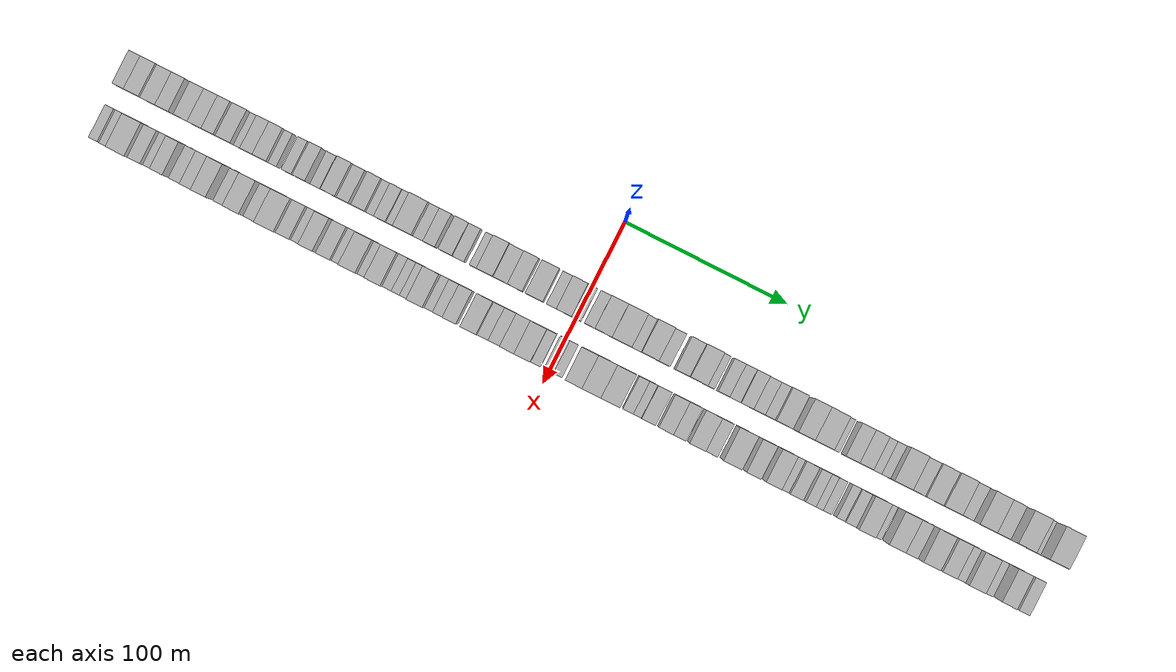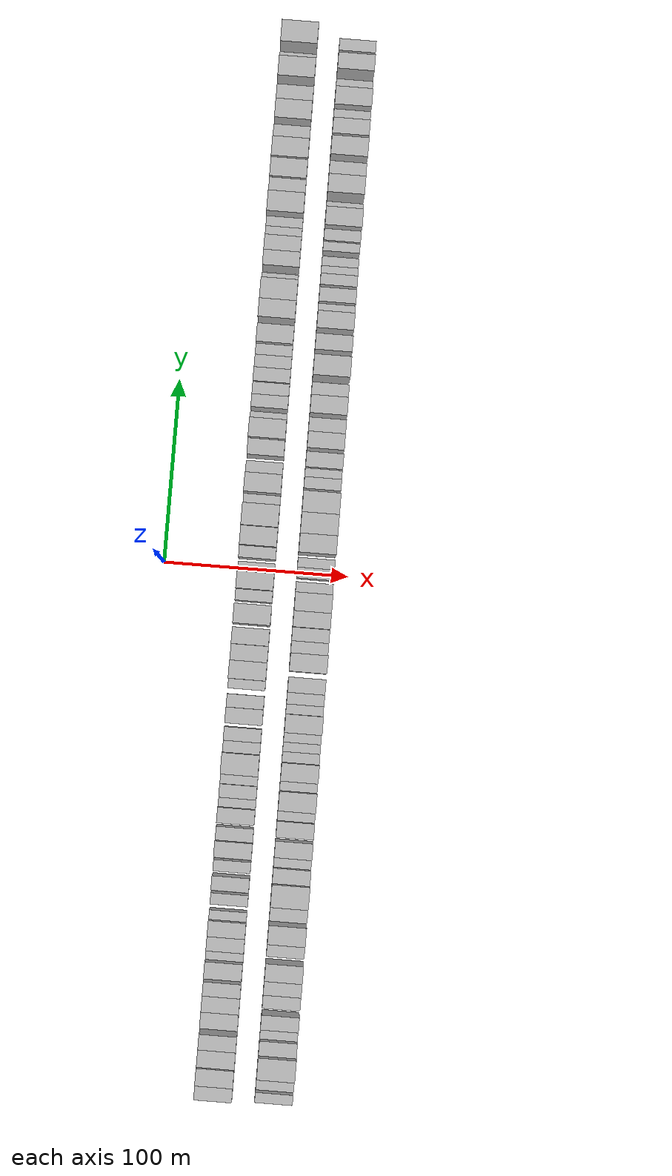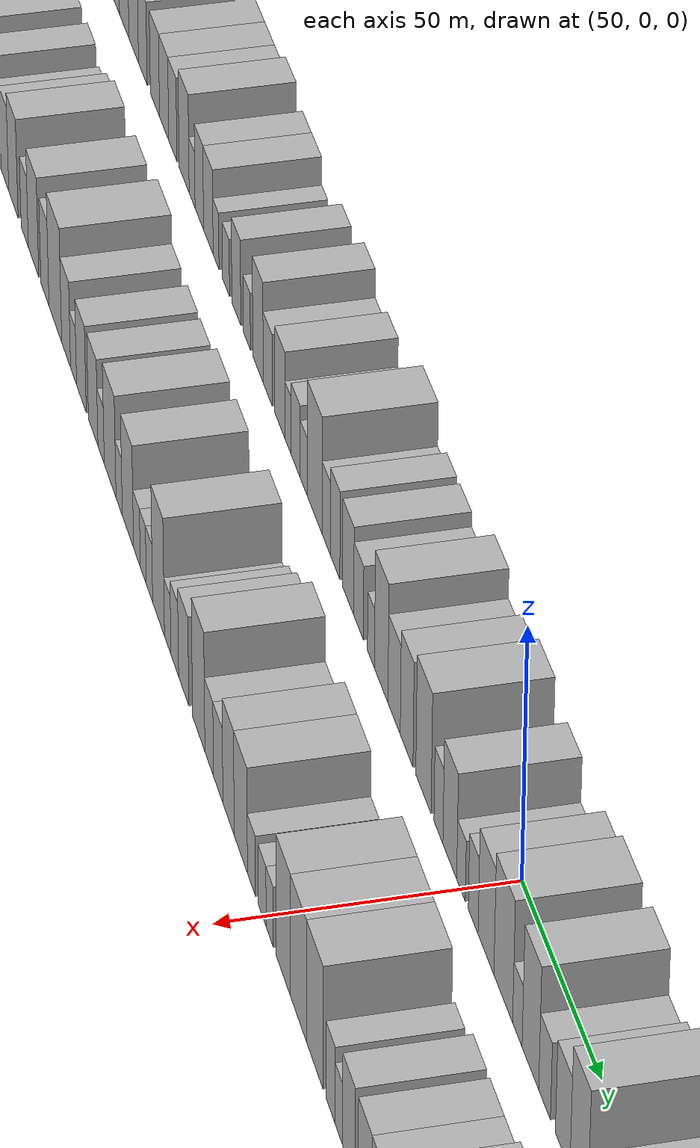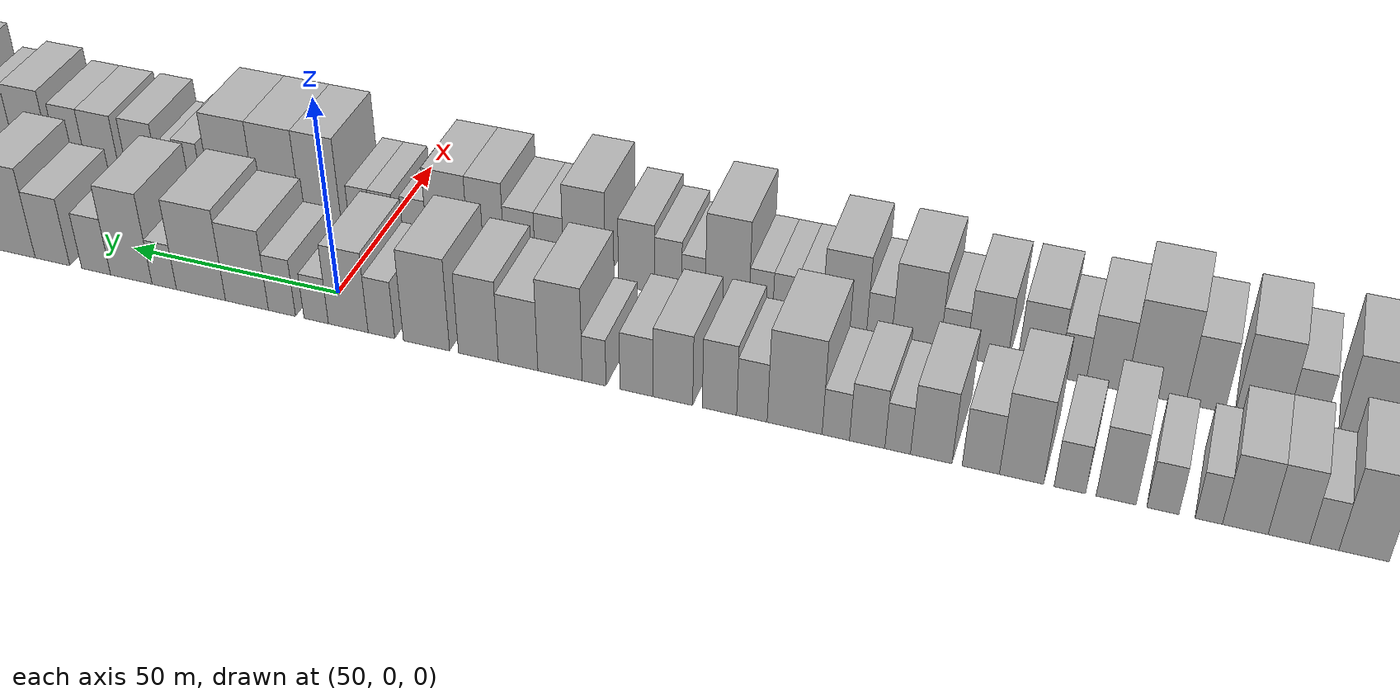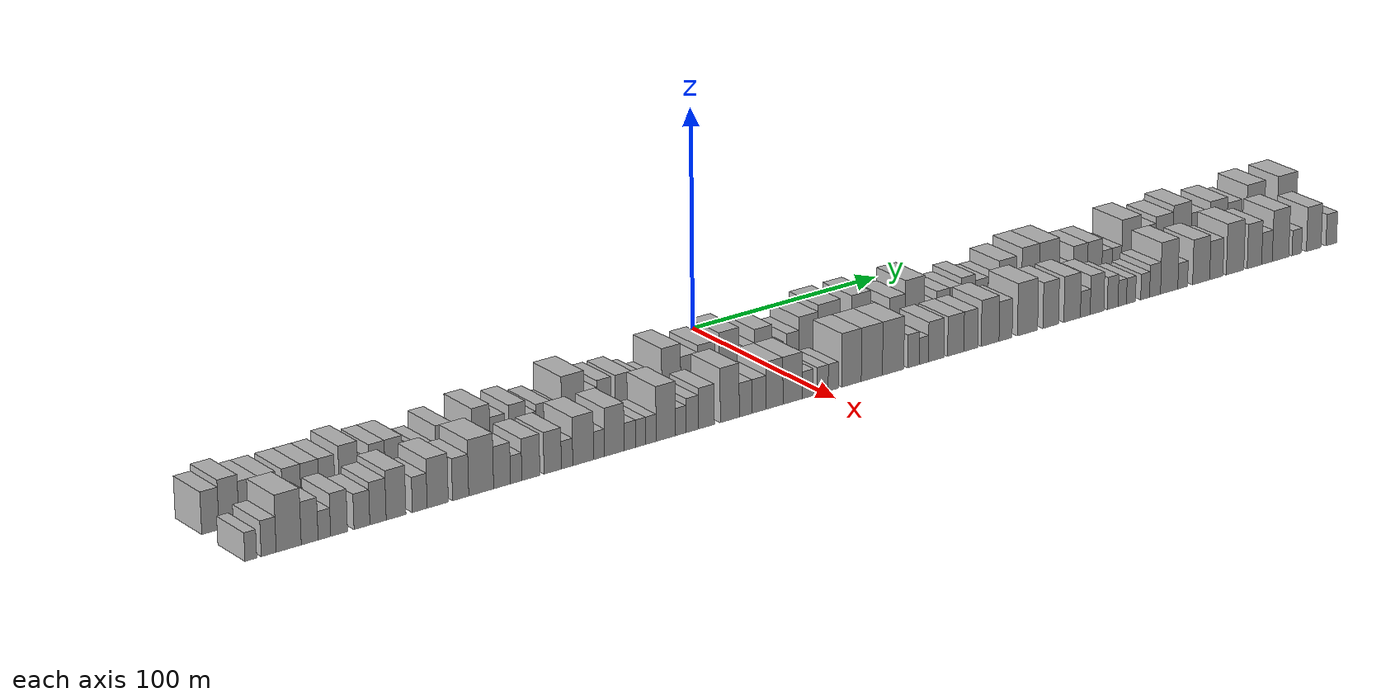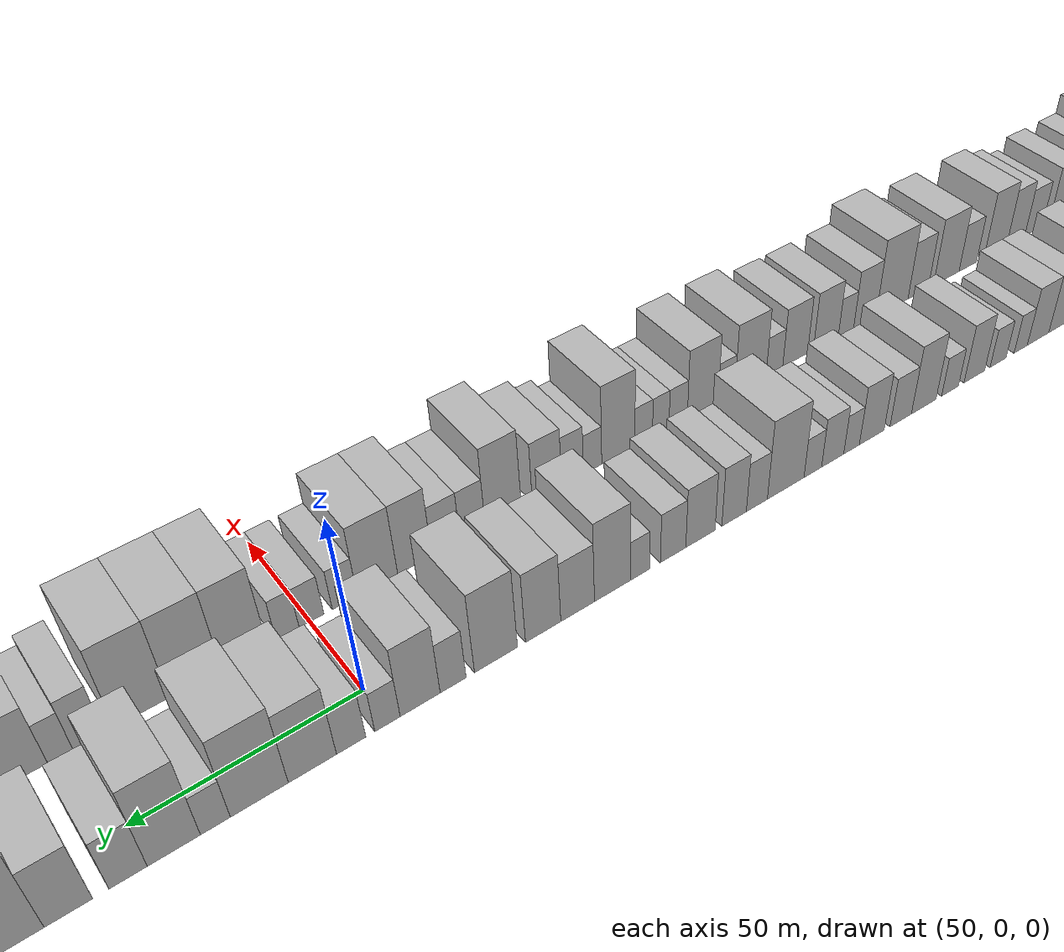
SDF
<sdf version="1.6">
 <world name="default">
  <scene>
   <sky><clouds><speed>12</speed></clouds></sky>
   <ambient>0.4 0.4 0.4 1</ambient>
   <background>0.7 0.7 0.7 1</background>
   <shadows>1</shadows>
  </scene>
  <gravity>0 0 -9.8066</gravity>
  <magnetic_field>6e-06 2.3e-05 -4.2e-05</magnetic_field>
  <physics default="0" name="default_physics" type="ode">
   <ode>
    <solver>
     <type>quick</type>
     <iters>10</iters>
     <sor>1.0</sor>
     <use_dynamic_moi_rescaling>0</use_dynamic_moi_rescaling>
    </solver>
    <constraints>
     <cfm>0</cfm>
     <erp>0.2</erp>
     <contact_max_correcting_vel>100</contact_max_correcting_vel>
     <contact_surface_layer>0.001</contact_surface_layer>
    </constraints>
   </ode>
   <max_step_size>0.004</max_step_size>
   <real_time_factor>1</real_time_factor>
   <real_time_update_rate>250</real_time_update_rate>
  </physics>
  <light name="sun" type="directional">
   <pose>0 0 10 0 0 0</pose>
   <diffuse>0.8 0.8 0.8 1</diffuse>
   <specular>0.2 0.2 0.2 1</specular>
   <attenuation>
    <range>1000</range>
    <constant>0.9</constant>
    <linear>0.01</linear>
    <quadratic>0.001</quadratic>
   </attenuation>
   <direction>-0.5 0.1 -0.9</direction>
  </light>
  <model name="building_1">
   <static>1</static>
   <pose>50.0000 -277.0836 0 0.000000 0.000000 0.000000</pose>
   <link name="link">
    <pose>0 0 9.00 0 0 0</pose>
    <collision name="collision"><geometry><box><size>20.0000 7.8328 18.0000</size></box></geometry></collision>
    <visual name="visual">
     <cast_shadows>0</cast_shadows>
     <geometry><box><size>20.0000 7.8328 18.0000</size></box></geometry>
     <material>
      <script>
       <uri>model://HANNAS_wall/materials/scripts</uri>
       <uri>model://HANNAS_wall/materials/textures</uri>
       <name>vrc/HANNAS_wall</name>
      </script>
     </material>
    </visual>
   </link>
  </model>
  <model name="building_2">
   <static>1</static>
   <pose>50.0000 -268.6406 0 0.000000 0.000000 0.000000</pose>
   <link name="link">
    <pose>0 0 10.50 0 0 0</pose>
    <collision name="collision"><geometry><box><size>20.0000 9.0533 21.0000</size></box></geometry></collision>
    <visual name="visual">
     <cast_shadows>0</cast_shadows>
     <geometry><box><size>20.0000 9.0533 21.0000</size></box></geometry>
     <material>
      <script>
       <uri>model://HANNAS_wall/materials/scripts</uri>
       <uri>model://HANNAS_wall/materials/textures</uri>
       <name>vrc/HANNAS_wall</name>
      </script>
     </material>
    </visual>
   </link>
  </model>
  <model name="building_3">
   <static>1</static>
   <pose>50.0000 -259.6193 0 0.000000 0.000000 0.000000</pose>
   <link name="link">
    <pose>0 0 9.00 0 0 0</pose>
    <collision name="collision"><geometry><box><size>20.0000 8.9893 18.0000</size></box></geometry></collision>
    <visual name="visual">
     <cast_shadows>0</cast_shadows>
     <geometry><box><size>20.0000 8.9893 18.0000</size></box></geometry>
     <material>
      <script>
       <uri>model://HANNAS_wall/materials/scripts</uri>
       <uri>model://HANNAS_wall/materials/textures</uri>
       <name>vrc/HANNAS_wall</name>
      </script>
     </material>
    </visual>
   </link>
  </model>
  <model name="building_4">
   <static>1</static>
   <pose>50.0000 -251.0663 0 0.000000 0.000000 0.000000</pose>
   <link name="link">
    <pose>0 0 9.00 0 0 0</pose>
    <collision name="collision"><geometry><box><size>20.0000 8.1167 18.0000</size></box></geometry></collision>
    <visual name="visual">
     <cast_shadows>0</cast_shadows>
     <geometry><box><size>20.0000 8.1167 18.0000</size></box></geometry>
     <material>
      <script>
       <uri>model://HANNAS_wall/materials/scripts</uri>
       <uri>model://HANNAS_wall/materials/textures</uri>
       <name>vrc/HANNAS_wall</name>
      </script>
     </material>
    </visual>
   </link>
  </model>
  <model name="building_5">
   <static>1</static>
   <pose>50.0000 -239.7565 0 0.000000 0.000000 0.000000</pose>
   <link name="link">
    <pose>0 0 9.00 0 0 0</pose>
    <collision name="collision"><geometry><box><size>20.0000 8.5028 18.0000</size></box></geometry></collision>
    <visual name="visual">
     <cast_shadows>0</cast_shadows>
     <geometry><box><size>20.0000 8.5028 18.0000</size></box></geometry>
     <material>
      <script>
       <uri>model://HANNAS_wall/materials/scripts</uri>
       <uri>model://HANNAS_wall/materials/textures</uri>
       <name>vrc/HANNAS_wall</name>
      </script>
     </material>
    </visual>
   </link>
  </model>
  <model name="building_6">
   <static>1</static>
   <pose>50.0000 -231.3192 0 0.000000 0.000000 0.000000</pose>
   <link name="link">
    <pose>0 0 9.00 0 0 0</pose>
    <collision name="collision"><geometry><box><size>20.0000 8.3718 18.0000</size></box></geometry></collision>
    <visual name="visual">
     <cast_shadows>0</cast_shadows>
     <geometry><box><size>20.0000 8.3718 18.0000</size></box></geometry>
     <material>
      <script>
       <uri>model://HANNAS_wall/materials/scripts</uri>
       <uri>model://HANNAS_wall/materials/textures</uri>
       <name>vrc/HANNAS_wall</name>
      </script>
     </material>
    </visual>
   </link>
  </model>
  <model name="building_7">
   <static>1</static>
   <pose>50.0000 -223.4350 0 0.000000 0.000000 0.000000</pose>
   <link name="link">
    <pose>0 0 9.00 0 0 0</pose>
    <collision name="collision"><geometry><box><size>20.0000 7.3966 18.0000</size></box></geometry></collision>
    <visual name="visual">
     <cast_shadows>0</cast_shadows>
     <geometry><box><size>20.0000 7.3966 18.0000</size></box></geometry>
     <material>
      <script>
       <uri>model://HANNAS_wall/materials/scripts</uri>
       <uri>model://HANNAS_wall/materials/textures</uri>
       <name>vrc/HANNAS_wall</name>
      </script>
     </material>
    </visual>
   </link>
  </model>
  <model name="building_8">
   <static>1</static>
   <pose>50.0000 -213.2876 0 0.000000 0.000000 0.000000</pose>
   <link name="link">
    <pose>0 0 10.50 0 0 0</pose>
    <collision name="collision"><geometry><box><size>20.0000 8.8982 21.0000</size></box></geometry></collision>
    <visual name="visual">
     <cast_shadows>0</cast_shadows>
     <geometry><box><size>20.0000 8.8982 21.0000</size></box></geometry>
     <material>
      <script>
       <uri>model://HANNAS_wall/materials/scripts</uri>
       <uri>model://HANNAS_wall/materials/textures</uri>
       <name>vrc/HANNAS_wall</name>
      </script>
     </material>
    </visual>
   </link>
  </model>
  <model name="building_9">
   <static>1</static>
   <pose>50.0000 -206.2193 0 0.000000 0.000000 0.000000</pose>
   <link name="link">
    <pose>0 0 6.00 0 0 0</pose>
    <collision name="collision"><geometry><box><size>20.0000 5.2385 12.0000</size></box></geometry></collision>
    <visual name="visual">
     <cast_shadows>0</cast_shadows>
     <geometry><box><size>20.0000 5.2385 12.0000</size></box></geometry>
     <material>
      <script>
       <uri>model://HANNAS_wall/materials/scripts</uri>
       <uri>model://HANNAS_wall/materials/textures</uri>
       <name>vrc/HANNAS_wall</name>
      </script>
     </material>
    </visual>
   </link>
  </model>
  <model name="building_10">
   <static>1</static>
   <pose>50.0000 -199.8635 0 0.000000 0.000000 0.000000</pose>
   <link name="link">
    <pose>0 0 9.00 0 0 0</pose>
    <collision name="collision"><geometry><box><size>20.0000 7.4730 18.0000</size></box></geometry></collision>
    <visual name="visual">
     <cast_shadows>0</cast_shadows>
     <geometry><box><size>20.0000 7.4730 18.0000</size></box></geometry>
     <material>
      <script>
       <uri>model://HANNAS_wall/materials/scripts</uri>
       <uri>model://HANNAS_wall/materials/textures</uri>
       <name>vrc/HANNAS_wall</name>
      </script>
     </material>
    </visual>
   </link>
  </model>
  <model name="building_11">
   <static>1</static>
   <pose>50.0000 -191.9743 0 0.000000 0.000000 0.000000</pose>
   <link name="link">
    <pose>0 0 9.00 0 0 0</pose>
    <collision name="collision"><geometry><box><size>20.0000 8.3054 18.0000</size></box></geometry></collision>
    <visual name="visual">
     <cast_shadows>0</cast_shadows>
     <geometry><box><size>20.0000 8.3054 18.0000</size></box></geometry>
     <material>
      <script>
       <uri>model://HANNAS_wall/materials/scripts</uri>
       <uri>model://HANNAS_wall/materials/textures</uri>
       <name>vrc/HANNAS_wall</name>
      </script>
     </material>
    </visual>
   </link>
  </model>
  <model name="building_12">
   <static>1</static>
   <pose>50.0000 -185.3072 0 0.000000 0.000000 0.000000</pose>
   <link name="link">
    <pose>0 0 6.00 0 0 0</pose>
    <collision name="collision"><geometry><box><size>20.0000 5.0287 12.0000</size></box></geometry></collision>
    <visual name="visual">
     <cast_shadows>0</cast_shadows>
     <geometry><box><size>20.0000 5.0287 12.0000</size></box></geometry>
     <material>
      <script>
       <uri>model://HANNAS_wall/materials/scripts</uri>
       <uri>model://HANNAS_wall/materials/textures</uri>
       <name>vrc/HANNAS_wall</name>
      </script>
     </material>
    </visual>
   </link>
  </model>
  <model name="building_13">
   <static>1</static>
   <pose>50.0000 -176.8049 0 0.000000 0.000000 0.000000</pose>
   <link name="link">
    <pose>0 0 6.00 0 0 0</pose>
    <collision name="collision"><geometry><box><size>20.0000 5.9760 12.0000</size></box></geometry></collision>
    <visual name="visual">
     <cast_shadows>0</cast_shadows>
     <geometry><box><size>20.0000 5.9760 12.0000</size></box></geometry>
     <material>
      <script>
       <uri>model://HANNAS_wall/materials/scripts</uri>
       <uri>model://HANNAS_wall/materials/textures</uri>
       <name>vrc/HANNAS_wall</name>
      </script>
     </material>
    </visual>
   </link>
  </model>
  <model name="building_14">
   <static>1</static>
   <pose>50.0000 -168.0518 0 0.000000 0.000000 0.000000</pose>
   <link name="link">
    <pose>0 0 9.00 0 0 0</pose>
    <collision name="collision"><geometry><box><size>20.0000 7.5302 18.0000</size></box></geometry></collision>
    <visual name="visual">
     <cast_shadows>0</cast_shadows>
     <geometry><box><size>20.0000 7.5302 18.0000</size></box></geometry>
     <material>
      <script>
       <uri>model://HANNAS_wall/materials/scripts</uri>
       <uri>model://HANNAS_wall/materials/textures</uri>
       <name>vrc/HANNAS_wall</name>
      </script>
     </material>
    </visual>
   </link>
  </model>
  <model name="building_15">
   <static>1</static>
   <pose>50.0000 -159.2871 0 0.000000 0.000000 0.000000</pose>
   <link name="link">
    <pose>0 0 6.00 0 0 0</pose>
    <collision name="collision"><geometry><box><size>20.0000 5.9992 12.0000</size></box></geometry></collision>
    <visual name="visual">
     <cast_shadows>0</cast_shadows>
     <geometry><box><size>20.0000 5.9992 12.0000</size></box></geometry>
     <material>
      <script>
       <uri>model://HANNAS_wall/materials/scripts</uri>
       <uri>model://HANNAS_wall/materials/textures</uri>
       <name>vrc/HANNAS_wall</name>
      </script>
     </material>
    </visual>
   </link>
  </model>
  <model name="building_16">
   <static>1</static>
   <pose>50.0000 -150.0109 0 0.000000 0.000000 0.000000</pose>
   <link name="link">
    <pose>0 0 10.50 0 0 0</pose>
    <collision name="collision"><geometry><box><size>20.0000 8.5532 21.0000</size></box></geometry></collision>
    <visual name="visual">
     <cast_shadows>0</cast_shadows>
     <geometry><box><size>20.0000 8.5532 21.0000</size></box></geometry>
     <material>
      <script>
       <uri>model://HANNAS_wall/materials/scripts</uri>
       <uri>model://HANNAS_wall/materials/textures</uri>
       <name>vrc/HANNAS_wall</name>
      </script>
     </material>
    </visual>
   </link>
  </model>
  <model name="building_17">
   <static>1</static>
   <pose>50.0000 -142.0953 0 0.000000 0.000000 0.000000</pose>
   <link name="link">
    <pose>0 0 7.50 0 0 0</pose>
    <collision name="collision"><geometry><box><size>20.0000 7.2780 15.0000</size></box></geometry></collision>
    <visual name="visual">
     <cast_shadows>0</cast_shadows>
     <geometry><box><size>20.0000 7.2780 15.0000</size></box></geometry>
     <material>
      <script>
       <uri>model://HANNAS_wall/materials/scripts</uri>
       <uri>model://HANNAS_wall/materials/textures</uri>
       <name>vrc/HANNAS_wall</name>
      </script>
     </material>
    </visual>
   </link>
  </model>
  <model name="building_18">
   <static>1</static>
   <pose>50.0000 -132.3448 0 0.000000 0.000000 0.000000</pose>
   <link name="link">
    <pose>0 0 9.00 0 0 0</pose>
    <collision name="collision"><geometry><box><size>20.0000 8.2228 18.0000</size></box></geometry></collision>
    <visual name="visual">
     <cast_shadows>0</cast_shadows>
     <geometry><box><size>20.0000 8.2228 18.0000</size></box></geometry>
     <material>
      <script>
       <uri>model://HANNAS_wall/materials/scripts</uri>
       <uri>model://HANNAS_wall/materials/textures</uri>
       <name>vrc/HANNAS_wall</name>
      </script>
     </material>
    </visual>
   </link>
  </model>
  <model name="building_19">
   <static>1</static>
   <pose>50.0000 -125.6786 0 0.000000 0.000000 0.000000</pose>
   <link name="link">
    <pose>0 0 6.00 0 0 0</pose>
    <collision name="collision"><geometry><box><size>20.0000 5.1096 12.0000</size></box></geometry></collision>
    <visual name="visual">
     <cast_shadows>0</cast_shadows>
     <geometry><box><size>20.0000 5.1096 12.0000</size></box></geometry>
     <material>
      <script>
       <uri>model://HANNAS_wall/materials/scripts</uri>
       <uri>model://HANNAS_wall/materials/textures</uri>
       <name>vrc/HANNAS_wall</name>
      </script>
     </material>
    </visual>
   </link>
  </model>
  <model name="building_20">
   <static>1</static>
   <pose>50.0000 -119.5632 0 0.000000 0.000000 0.000000</pose>
   <link name="link">
    <pose>0 0 7.50 0 0 0</pose>
    <collision name="collision"><geometry><box><size>20.0000 7.1214 15.0000</size></box></geometry></collision>
    <visual name="visual">
     <cast_shadows>0</cast_shadows>
     <geometry><box><size>20.0000 7.1214 15.0000</size></box></geometry>
     <material>
      <script>
       <uri>model://HANNAS_wall/materials/scripts</uri>
       <uri>model://HANNAS_wall/materials/textures</uri>
       <name>vrc/HANNAS_wall</name>
      </script>
     </material>
    </visual>
   </link>
  </model>
  <model name="building_21">
   <static>1</static>
   <pose>50.0000 -113.2214 0 0.000000 0.000000 0.000000</pose>
   <link name="link">
    <pose>0 0 6.00 0 0 0</pose>
    <collision name="collision"><geometry><box><size>20.0000 5.5622 12.0000</size></box></geometry></collision>
    <visual name="visual">
     <cast_shadows>0</cast_shadows>
     <geometry><box><size>20.0000 5.5622 12.0000</size></box></geometry>
     <material>
      <script>
       <uri>model://HANNAS_wall/materials/scripts</uri>
       <uri>model://HANNAS_wall/materials/textures</uri>
       <name>vrc/HANNAS_wall</name>
      </script>
     </material>
    </visual>
   </link>
  </model>
  <model name="building_22">
   <static>1</static>
   <pose>50.0000 -104.7988 0 0.000000 0.000000 0.000000</pose>
   <link name="link">
    <pose>0 0 12.00 0 0 0</pose>
    <collision name="collision"><geometry><box><size>20.0000 11.2829 24.0000</size></box></geometry></collision>
    <visual name="visual">
     <cast_shadows>0</cast_shadows>
     <geometry><box><size>20.0000 11.2829 24.0000</size></box></geometry>
     <material>
      <script>
       <uri>model://HANNAS_wall/materials/scripts</uri>
       <uri>model://HANNAS_wall/materials/textures</uri>
       <name>vrc/HANNAS_wall</name>
      </script>
     </material>
    </visual>
   </link>
  </model>
  <model name="building_23">
   <static>1</static>
   <pose>50.0000 -95.9924 0 0.000000 0.000000 0.000000</pose>
   <link name="link">
    <pose>0 0 7.50 0 0 0</pose>
    <collision name="collision"><geometry><box><size>20.0000 6.3301 15.0000</size></box></geometry></collision>
    <visual name="visual">
     <cast_shadows>0</cast_shadows>
     <geometry><box><size>20.0000 6.3301 15.0000</size></box></geometry>
     <material>
      <script>
       <uri>model://HANNAS_wall/materials/scripts</uri>
       <uri>model://HANNAS_wall/materials/textures</uri>
       <name>vrc/HANNAS_wall</name>
      </script>
     </material>
    </visual>
   </link>
  </model>
  <model name="building_24">
   <static>1</static>
   <pose>50.0000 -89.2120 0 0.000000 0.000000 0.000000</pose>
   <link name="link">
    <pose>0 0 9.00 0 0 0</pose>
    <collision name="collision"><geometry><box><size>20.0000 7.2307 18.0000</size></box></geometry></collision>
    <visual name="visual">
     <cast_shadows>0</cast_shadows>
     <geometry><box><size>20.0000 7.2307 18.0000</size></box></geometry>
     <material>
      <script>
       <uri>model://HANNAS_wall/materials/scripts</uri>
       <uri>model://HANNAS_wall/materials/textures</uri>
       <name>vrc/HANNAS_wall</name>
      </script>
     </material>
    </visual>
   </link>
  </model>
  <model name="building_25">
   <static>1</static>
   <pose>50.0000 -79.4001 0 0.000000 0.000000 0.000000</pose>
   <link name="link">
    <pose>0 0 9.00 0 0 0</pose>
    <collision name="collision"><geometry><box><size>20.0000 8.3930 18.0000</size></box></geometry></collision>
    <visual name="visual">
     <cast_shadows>0</cast_shadows>
     <geometry><box><size>20.0000 8.3930 18.0000</size></box></geometry>
     <material>
      <script>
       <uri>model://HANNAS_wall/materials/scripts</uri>
       <uri>model://HANNAS_wall/materials/textures</uri>
       <name>vrc/HANNAS_wall</name>
      </script>
     </material>
    </visual>
   </link>
  </model>
  <model name="building_26">
   <static>1</static>
   <pose>50.0000 -71.6414 0 0.000000 0.000000 0.000000</pose>
   <link name="link">
    <pose>0 0 7.50 0 0 0</pose>
    <collision name="collision"><geometry><box><size>20.0000 7.1246 15.0000</size></box></geometry></collision>
    <visual name="visual">
     <cast_shadows>0</cast_shadows>
     <geometry><box><size>20.0000 7.1246 15.0000</size></box></geometry>
     <material>
      <script>
       <uri>model://HANNAS_wall/materials/scripts</uri>
       <uri>model://HANNAS_wall/materials/textures</uri>
       <name>vrc/HANNAS_wall</name>
      </script>
     </material>
    </visual>
   </link>
  </model>
  <model name="building_27">
   <static>1</static>
   <pose>50.0000 -62.5019 0 0.000000 0.000000 0.000000</pose>
   <link name="link">
    <pose>0 0 6.00 0 0 0</pose>
    <collision name="collision"><geometry><box><size>20.0000 5.1543 12.0000</size></box></geometry></collision>
    <visual name="visual">
     <cast_shadows>0</cast_shadows>
     <geometry><box><size>20.0000 5.1543 12.0000</size></box></geometry>
     <material>
      <script>
       <uri>model://HANNAS_wall/materials/scripts</uri>
       <uri>model://HANNAS_wall/materials/textures</uri>
       <name>vrc/HANNAS_wall</name>
      </script>
     </material>
    </visual>
   </link>
  </model>
  <model name="building_28">
   <static>1</static>
   <pose>50.0000 -55.0729 0 0.000000 0.000000 0.000000</pose>
   <link name="link">
    <pose>0 0 12.00 0 0 0</pose>
    <collision name="collision"><geometry><box><size>20.0000 9.7038 24.0000</size></box></geometry></collision>
    <visual name="visual">
     <cast_shadows>0</cast_shadows>
     <geometry><box><size>20.0000 9.7038 24.0000</size></box></geometry>
     <material>
      <script>
       <uri>model://HANNAS_wall/materials/scripts</uri>
       <uri>model://HANNAS_wall/materials/textures</uri>
       <name>vrc/HANNAS_wall</name>
      </script>
     </material>
    </visual>
   </link>
  </model>
  <model name="building_29">
   <static>1</static>
   <pose>50.0000 -45.8381 0 0.000000 0.000000 0.000000</pose>
   <link name="link">
    <pose>0 0 9.00 0 0 0</pose>
    <collision name="collision"><geometry><box><size>20.0000 8.7659 18.0000</size></box></geometry></collision>
    <visual name="visual">
     <cast_shadows>0</cast_shadows>
     <geometry><box><size>20.0000 8.7659 18.0000</size></box></geometry>
     <material>
      <script>
       <uri>model://HANNAS_wall/materials/scripts</uri>
       <uri>model://HANNAS_wall/materials/textures</uri>
       <name>vrc/HANNAS_wall</name>
      </script>
     </material>
    </visual>
   </link>
  </model>
  <model name="building_30">
   <static>1</static>
   <pose>50.0000 -36.9854 0 0.000000 0.000000 0.000000</pose>
   <link name="link">
    <pose>0 0 10.50 0 0 0</pose>
    <collision name="collision"><geometry><box><size>20.0000 8.9395 21.0000</size></box></geometry></collision>
    <visual name="visual">
     <cast_shadows>0</cast_shadows>
     <geometry><box><size>20.0000 8.9395 21.0000</size></box></geometry>
     <material>
      <script>
       <uri>model://HANNAS_wall/materials/scripts</uri>
       <uri>model://HANNAS_wall/materials/textures</uri>
       <name>vrc/HANNAS_wall</name>
      </script>
     </material>
    </visual>
   </link>
  </model>
  <model name="building_31">
   <static>1</static>
   <pose>50.0000 -25.2559 0 0.000000 0.000000 0.000000</pose>
   <link name="link">
    <pose>0 0 12.00 0 0 0</pose>
    <collision name="collision"><geometry><box><size>20.0000 10.5196 24.0000</size></box></geometry></collision>
    <visual name="visual">
     <cast_shadows>0</cast_shadows>
     <geometry><box><size>20.0000 10.5196 24.0000</size></box></geometry>
     <material>
      <script>
       <uri>model://HANNAS_wall/materials/scripts</uri>
       <uri>model://HANNAS_wall/materials/textures</uri>
       <name>vrc/HANNAS_wall</name>
      </script>
     </material>
    </visual>
   </link>
  </model>
  <model name="building_32">
   <static>1</static>
   <pose>50.0000 -14.9282 0 0.000000 0.000000 0.000000</pose>
   <link name="link">
    <pose>0 0 7.50 0 0 0</pose>
    <collision name="collision"><geometry><box><size>20.0000 6.1357 15.0000</size></box></geometry></collision>
    <visual name="visual">
     <cast_shadows>0</cast_shadows>
     <geometry><box><size>20.0000 6.1357 15.0000</size></box></geometry>
     <material>
      <script>
       <uri>model://HANNAS_wall/materials/scripts</uri>
       <uri>model://HANNAS_wall/materials/textures</uri>
       <name>vrc/HANNAS_wall</name>
      </script>
     </material>
    </visual>
   </link>
  </model>
  <model name="building_33">
   <static>1</static>
   <pose>50.0000 -7.2381 0 0.000000 0.000000 0.000000</pose>
   <link name="link">
    <pose>0 0 10.50 0 0 0</pose>
    <collision name="collision"><geometry><box><size>20.0000 9.2446 21.0000</size></box></geometry></collision>
    <visual name="visual">
     <cast_shadows>0</cast_shadows>
     <geometry><box><size>20.0000 9.2446 21.0000</size></box></geometry>
     <material>
      <script>
       <uri>model://HANNAS_wall/materials/scripts</uri>
       <uri>model://HANNAS_wall/materials/textures</uri>
       <name>vrc/HANNAS_wall</name>
      </script>
     </material>
    </visual>
   </link>
  </model>
  <model name="building_34">
   <static>1</static>
   <pose>50.0000 0.2510 0 0.000000 0.000000 0.000000</pose>
   <link name="link">
    <pose>0 0 6.00 0 0 0</pose>
    <collision name="collision"><geometry><box><size>20.0000 5.7335 12.0000</size></box></geometry></collision>
    <visual name="visual">
     <cast_shadows>0</cast_shadows>
     <geometry><box><size>20.0000 5.7335 12.0000</size></box></geometry>
     <material>
      <script>
       <uri>model://HANNAS_wall/materials/scripts</uri>
       <uri>model://HANNAS_wall/materials/textures</uri>
       <name>vrc/HANNAS_wall</name>
      </script>
     </material>
    </visual>
   </link>
  </model>
  <model name="building_35">
   <static>1</static>
   <pose>50.0000 8.3364 0 0.000000 0.000000 0.000000</pose>
   <link name="link">
    <pose>0 0 7.50 0 0 0</pose>
    <collision name="collision"><geometry><box><size>20.0000 6.4373 15.0000</size></box></geometry></collision>
    <visual name="visual">
     <cast_shadows>0</cast_shadows>
     <geometry><box><size>20.0000 6.4373 15.0000</size></box></geometry>
     <material>
      <script>
       <uri>model://HANNAS_wall/materials/scripts</uri>
       <uri>model://HANNAS_wall/materials/textures</uri>
       <name>vrc/HANNAS_wall</name>
      </script>
     </material>
    </visual>
   </link>
  </model>
  <model name="building_36">
   <static>1</static>
   <pose>50.0000 16.7058 0 0.000000 0.000000 0.000000</pose>
   <link name="link">
    <pose>0 0 10.50 0 0 0</pose>
    <collision name="collision"><geometry><box><size>20.0000 10.3015 21.0000</size></box></geometry></collision>
    <visual name="visual">
     <cast_shadows>0</cast_shadows>
     <geometry><box><size>20.0000 10.3015 21.0000</size></box></geometry>
     <material>
      <script>
       <uri>model://HANNAS_wall/materials/scripts</uri>
       <uri>model://HANNAS_wall/materials/textures</uri>
       <name>vrc/HANNAS_wall</name>
      </script>
     </material>
    </visual>
   </link>
  </model>
  <model name="building_37">
   <static>1</static>
   <pose>50.0000 27.8285 0 0.000000 0.000000 0.000000</pose>
   <link name="link">
    <pose>0 0 12.00 0 0 0</pose>
    <collision name="collision"><geometry><box><size>20.0000 11.9438 24.0000</size></box></geometry></collision>
    <visual name="visual">
     <cast_shadows>0</cast_shadows>
     <geometry><box><size>20.0000 11.9438 24.0000</size></box></geometry>
     <material>
      <script>
       <uri>model://HANNAS_wall/materials/scripts</uri>
       <uri>model://HANNAS_wall/materials/textures</uri>
       <name>vrc/HANNAS_wall</name>
      </script>
     </material>
    </visual>
   </link>
  </model>
  <model name="building_38">
   <static>1</static>
   <pose>50.0000 36.7897 0 0.000000 0.000000 0.000000</pose>
   <link name="link">
    <pose>0 0 6.00 0 0 0</pose>
    <collision name="collision"><geometry><box><size>20.0000 5.9785 12.0000</size></box></geometry></collision>
    <visual name="visual">
     <cast_shadows>0</cast_shadows>
     <geometry><box><size>20.0000 5.9785 12.0000</size></box></geometry>
     <material>
      <script>
       <uri>model://HANNAS_wall/materials/scripts</uri>
       <uri>model://HANNAS_wall/materials/textures</uri>
       <name>vrc/HANNAS_wall</name>
      </script>
     </material>
    </visual>
   </link>
  </model>
  <model name="building_39">
   <static>1</static>
   <pose>50.0000 44.9411 0 0.000000 0.000000 0.000000</pose>
   <link name="link">
    <pose>0 0 12.00 0 0 0</pose>
    <collision name="collision"><geometry><box><size>20.0000 10.3244 24.0000</size></box></geometry></collision>
    <visual name="visual">
     <cast_shadows>0</cast_shadows>
     <geometry><box><size>20.0000 10.3244 24.0000</size></box></geometry>
     <material>
      <script>
       <uri>model://HANNAS_wall/materials/scripts</uri>
       <uri>model://HANNAS_wall/materials/textures</uri>
       <name>vrc/HANNAS_wall</name>
      </script>
     </material>
    </visual>
   </link>
  </model>
  <model name="building_40">
   <static>1</static>
   <pose>50.0000 53.7202 0 0.000000 0.000000 0.000000</pose>
   <link name="link">
    <pose>0 0 7.50 0 0 0</pose>
    <collision name="collision"><geometry><box><size>20.0000 7.2339 15.0000</size></box></geometry></collision>
    <visual name="visual">
     <cast_shadows>0</cast_shadows>
     <geometry><box><size>20.0000 7.2339 15.0000</size></box></geometry>
     <material>
      <script>
       <uri>model://HANNAS_wall/materials/scripts</uri>
       <uri>model://HANNAS_wall/materials/textures</uri>
       <name>vrc/HANNAS_wall</name>
      </script>
     </material>
    </visual>
   </link>
  </model>
  <model name="building_41">
   <static>1</static>
   <pose>50.0000 64.7341 0 0.000000 0.000000 0.000000</pose>
   <link name="link">
    <pose>0 0 9.00 0 0 0</pose>
    <collision name="collision"><geometry><box><size>20.0000 8.7940 18.0000</size></box></geometry></collision>
    <visual name="visual">
     <cast_shadows>0</cast_shadows>
     <geometry><box><size>20.0000 8.7940 18.0000</size></box></geometry>
     <material>
      <script>
       <uri>model://HANNAS_wall/materials/scripts</uri>
       <uri>model://HANNAS_wall/materials/textures</uri>
       <name>vrc/HANNAS_wall</name>
      </script>
     </material>
    </visual>
   </link>
  </model>
  <model name="building_42">
   <static>1</static>
   <pose>50.0000 74.3640 0 0.000000 0.000000 0.000000</pose>
   <link name="link">
    <pose>0 0 12.00 0 0 0</pose>
    <collision name="collision"><geometry><box><size>20.0000 10.4658 24.0000</size></box></geometry></collision>
    <visual name="visual">
     <cast_shadows>0</cast_shadows>
     <geometry><box><size>20.0000 10.4658 24.0000</size></box></geometry>
     <material>
      <script>
       <uri>model://HANNAS_wall/materials/scripts</uri>
       <uri>model://HANNAS_wall/materials/textures</uri>
       <name>vrc/HANNAS_wall</name>
      </script>
     </material>
    </visual>
   </link>
  </model>
  <model name="building_43">
   <static>1</static>
   <pose>50.0000 82.0531 0 0.000000 0.000000 0.000000</pose>
   <link name="link">
    <pose>0 0 6.00 0 0 0</pose>
    <collision name="collision"><geometry><box><size>20.0000 4.9122 12.0000</size></box></geometry></collision>
    <visual name="visual">
     <cast_shadows>0</cast_shadows>
     <geometry><box><size>20.0000 4.9122 12.0000</size></box></geometry>
     <material>
      <script>
       <uri>model://HANNAS_wall/materials/scripts</uri>
       <uri>model://HANNAS_wall/materials/textures</uri>
       <name>vrc/HANNAS_wall</name>
      </script>
     </material>
    </visual>
   </link>
  </model>
  <model name="building_44">
   <static>1</static>
   <pose>50.0000 90.0316 0 0.000000 0.000000 0.000000</pose>
   <link name="link">
    <pose>0 0 7.50 0 0 0</pose>
    <collision name="collision"><geometry><box><size>20.0000 7.0448 15.0000</size></box></geometry></collision>
    <visual name="visual">
     <cast_shadows>0</cast_shadows>
     <geometry><box><size>20.0000 7.0448 15.0000</size></box></geometry>
     <material>
      <script>
       <uri>model://HANNAS_wall/materials/scripts</uri>
       <uri>model://HANNAS_wall/materials/textures</uri>
       <name>vrc/HANNAS_wall</name>
      </script>
     </material>
    </visual>
   </link>
  </model>
  <model name="building_45">
   <static>1</static>
   <pose>50.0000 96.8660 0 0.000000 0.000000 0.000000</pose>
   <link name="link">
    <pose>0 0 7.50 0 0 0</pose>
    <collision name="collision"><geometry><box><size>20.0000 6.6240 15.0000</size></box></geometry></collision>
    <visual name="visual">
     <cast_shadows>0</cast_shadows>
     <geometry><box><size>20.0000 6.6240 15.0000</size></box></geometry>
     <material>
      <script>
       <uri>model://HANNAS_wall/materials/scripts</uri>
       <uri>model://HANNAS_wall/materials/textures</uri>
       <name>vrc/HANNAS_wall</name>
      </script>
     </material>
    </visual>
   </link>
  </model>
  <model name="building_46">
   <static>1</static>
   <pose>50.0000 103.9636 0 0.000000 0.000000 0.000000</pose>
   <link name="link">
    <pose>0 0 9.00 0 0 0</pose>
    <collision name="collision"><geometry><box><size>20.0000 7.5711 18.0000</size></box></geometry></collision>
    <visual name="visual">
     <cast_shadows>0</cast_shadows>
     <geometry><box><size>20.0000 7.5711 18.0000</size></box></geometry>
     <material>
      <script>
       <uri>model://HANNAS_wall/materials/scripts</uri>
       <uri>model://HANNAS_wall/materials/textures</uri>
       <name>vrc/HANNAS_wall</name>
      </script>
     </material>
    </visual>
   </link>
  </model>
  <model name="building_47">
   <static>1</static>
   <pose>50.0000 111.4161 0 0.000000 0.000000 0.000000</pose>
   <link name="link">
    <pose>0 0 7.50 0 0 0</pose>
    <collision name="collision"><geometry><box><size>20.0000 7.3340 15.0000</size></box></geometry></collision>
    <visual name="visual">
     <cast_shadows>0</cast_shadows>
     <geometry><box><size>20.0000 7.3340 15.0000</size></box></geometry>
     <material>
      <script>
       <uri>model://HANNAS_wall/materials/scripts</uri>
       <uri>model://HANNAS_wall/materials/textures</uri>
       <name>vrc/HANNAS_wall</name>
      </script>
     </material>
    </visual>
   </link>
  </model>
  <model name="building_48">
   <static>1</static>
   <pose>50.0000 118.0838 0 0.000000 0.000000 0.000000</pose>
   <link name="link">
    <pose>0 0 7.50 0 0 0</pose>
    <collision name="collision"><geometry><box><size>20.0000 6.0014 15.0000</size></box></geometry></collision>
    <visual name="visual">
     <cast_shadows>0</cast_shadows>
     <geometry><box><size>20.0000 6.0014 15.0000</size></box></geometry>
     <material>
      <script>
       <uri>model://HANNAS_wall/materials/scripts</uri>
       <uri>model://HANNAS_wall/materials/textures</uri>
       <name>vrc/HANNAS_wall</name>
      </script>
     </material>
    </visual>
   </link>
  </model>
  <model name="building_49">
   <static>1</static>
   <pose>50.0000 126.0789 0 0.000000 0.000000 0.000000</pose>
   <link name="link">
    <pose>0 0 10.50 0 0 0</pose>
    <collision name="collision"><geometry><box><size>20.0000 9.9887 21.0000</size></box></geometry></collision>
    <visual name="visual">
     <cast_shadows>0</cast_shadows>
     <geometry><box><size>20.0000 9.9887 21.0000</size></box></geometry>
     <material>
      <script>
       <uri>model://HANNAS_wall/materials/scripts</uri>
       <uri>model://HANNAS_wall/materials/textures</uri>
       <name>vrc/HANNAS_wall</name>
      </script>
     </material>
    </visual>
   </link>
  </model>
  <model name="building_50">
   <static>1</static>
   <pose>50.0000 139.0721 0 0.000000 0.000000 0.000000</pose>
   <link name="link">
    <pose>0 0 12.00 0 0 0</pose>
    <collision name="collision"><geometry><box><size>20.0000 9.9978 24.0000</size></box></geometry></collision>
    <visual name="visual">
     <cast_shadows>0</cast_shadows>
     <geometry><box><size>20.0000 9.9978 24.0000</size></box></geometry>
     <material>
      <script>
       <uri>model://HANNAS_wall/materials/scripts</uri>
       <uri>model://HANNAS_wall/materials/textures</uri>
       <name>vrc/HANNAS_wall</name>
      </script>
     </material>
    </visual>
   </link>
  </model>
  <model name="building_51">
   <static>1</static>
   <pose>50.0000 149.7986 0 0.000000 0.000000 0.000000</pose>
   <link name="link">
    <pose>0 0 12.00 0 0 0</pose>
    <collision name="collision"><geometry><box><size>20.0000 11.4551 24.0000</size></box></geometry></collision>
    <visual name="visual">
     <cast_shadows>0</cast_shadows>
     <geometry><box><size>20.0000 11.4551 24.0000</size></box></geometry>
     <material>
      <script>
       <uri>model://HANNAS_wall/materials/scripts</uri>
       <uri>model://HANNAS_wall/materials/textures</uri>
       <name>vrc/HANNAS_wall</name>
      </script>
     </material>
    </visual>
   </link>
  </model>
  <model name="building_52">
   <static>1</static>
   <pose>50.0000 158.0299 0 0.000000 0.000000 0.000000</pose>
   <link name="link">
    <pose>0 0 6.00 0 0 0</pose>
    <collision name="collision"><geometry><box><size>20.0000 5.0075 12.0000</size></box></geometry></collision>
    <visual name="visual">
     <cast_shadows>0</cast_shadows>
     <geometry><box><size>20.0000 5.0075 12.0000</size></box></geometry>
     <material>
      <script>
       <uri>model://HANNAS_wall/materials/scripts</uri>
       <uri>model://HANNAS_wall/materials/textures</uri>
       <name>vrc/HANNAS_wall</name>
      </script>
     </material>
    </visual>
   </link>
  </model>
  <model name="building_53">
   <static>1</static>
   <pose>50.0000 167.7254 0 0.000000 0.000000 0.000000</pose>
   <link name="link">
    <pose>0 0 9.00 0 0 0</pose>
    <collision name="collision"><geometry><box><size>20.0000 8.3835 18.0000</size></box></geometry></collision>
    <visual name="visual">
     <cast_shadows>0</cast_shadows>
     <geometry><box><size>20.0000 8.3835 18.0000</size></box></geometry>
     <material>
      <script>
       <uri>model://HANNAS_wall/materials/scripts</uri>
       <uri>model://HANNAS_wall/materials/textures</uri>
       <name>vrc/HANNAS_wall</name>
      </script>
     </material>
    </visual>
   </link>
  </model>
  <model name="building_54">
   <static>1</static>
   <pose>50.0000 176.0990 0 0.000000 0.000000 0.000000</pose>
   <link name="link">
    <pose>0 0 9.00 0 0 0</pose>
    <collision name="collision"><geometry><box><size>20.0000 8.3637 18.0000</size></box></geometry></collision>
    <visual name="visual">
     <cast_shadows>0</cast_shadows>
     <geometry><box><size>20.0000 8.3637 18.0000</size></box></geometry>
     <material>
      <script>
       <uri>model://HANNAS_wall/materials/scripts</uri>
       <uri>model://HANNAS_wall/materials/textures</uri>
       <name>vrc/HANNAS_wall</name>
      </script>
     </material>
    </visual>
   </link>
  </model>
  <model name="building_55">
   <static>1</static>
   <pose>50.0000 183.2807 0 0.000000 0.000000 0.000000</pose>
   <link name="link">
    <pose>0 0 6.00 0 0 0</pose>
    <collision name="collision"><geometry><box><size>20.0000 5.9995 12.0000</size></box></geometry></collision>
    <visual name="visual">
     <cast_shadows>0</cast_shadows>
     <geometry><box><size>20.0000 5.9995 12.0000</size></box></geometry>
     <material>
      <script>
       <uri>model://HANNAS_wall/materials/scripts</uri>
       <uri>model://HANNAS_wall/materials/textures</uri>
       <name>vrc/HANNAS_wall</name>
      </script>
     </material>
    </visual>
   </link>
  </model>
  <model name="building_56">
   <static>1</static>
   <pose>50.0000 189.0195 0 0.000000 0.000000 0.000000</pose>
   <link name="link">
    <pose>0 0 6.00 0 0 0</pose>
    <collision name="collision"><geometry><box><size>20.0000 5.4782 12.0000</size></box></geometry></collision>
    <visual name="visual">
     <cast_shadows>0</cast_shadows>
     <geometry><box><size>20.0000 5.4782 12.0000</size></box></geometry>
     <material>
      <script>
       <uri>model://HANNAS_wall/materials/scripts</uri>
       <uri>model://HANNAS_wall/materials/textures</uri>
       <name>vrc/HANNAS_wall</name>
      </script>
     </material>
    </visual>
   </link>
  </model>
  <model name="building_57">
   <static>1</static>
   <pose>50.0000 197.3581 0 0.000000 0.000000 0.000000</pose>
   <link name="link">
    <pose>0 0 12.00 0 0 0</pose>
    <collision name="collision"><geometry><box><size>20.0000 11.1989 24.0000</size></box></geometry></collision>
    <visual name="visual">
     <cast_shadows>0</cast_shadows>
     <geometry><box><size>20.0000 11.1989 24.0000</size></box></geometry>
     <material>
      <script>
       <uri>model://HANNAS_wall/materials/scripts</uri>
       <uri>model://HANNAS_wall/materials/textures</uri>
       <name>vrc/HANNAS_wall</name>
      </script>
     </material>
    </visual>
   </link>
  </model>
  <model name="building_58">
   <static>1</static>
   <pose>50.0000 207.3073 0 0.000000 0.000000 0.000000</pose>
   <link name="link">
    <pose>0 0 9.00 0 0 0</pose>
    <collision name="collision"><geometry><box><size>20.0000 8.6995 18.0000</size></box></geometry></collision>
    <visual name="visual">
     <cast_shadows>0</cast_shadows>
     <geometry><box><size>20.0000 8.6995 18.0000</size></box></geometry>
     <material>
      <script>
       <uri>model://HANNAS_wall/materials/scripts</uri>
       <uri>model://HANNAS_wall/materials/textures</uri>
       <name>vrc/HANNAS_wall</name>
      </script>
     </material>
    </visual>
   </link>
  </model>
  <model name="building_59">
   <static>1</static>
   <pose>50.0000 216.8353 0 0.000000 0.000000 0.000000</pose>
   <link name="link">
    <pose>0 0 10.50 0 0 0</pose>
    <collision name="collision"><geometry><box><size>20.0000 10.3565 21.0000</size></box></geometry></collision>
    <visual name="visual">
     <cast_shadows>0</cast_shadows>
     <geometry><box><size>20.0000 10.3565 21.0000</size></box></geometry>
     <material>
      <script>
       <uri>model://HANNAS_wall/materials/scripts</uri>
       <uri>model://HANNAS_wall/materials/textures</uri>
       <name>vrc/HANNAS_wall</name>
      </script>
     </material>
    </visual>
   </link>
  </model>
  <model name="building_60">
   <static>1</static>
   <pose>50.0000 227.3803 0 0.000000 0.000000 0.000000</pose>
   <link name="link">
    <pose>0 0 12.00 0 0 0</pose>
    <collision name="collision"><geometry><box><size>20.0000 10.7336 24.0000</size></box></geometry></collision>
    <visual name="visual">
     <cast_shadows>0</cast_shadows>
     <geometry><box><size>20.0000 10.7336 24.0000</size></box></geometry>
     <material>
      <script>
       <uri>model://HANNAS_wall/materials/scripts</uri>
       <uri>model://HANNAS_wall/materials/textures</uri>
       <name>vrc/HANNAS_wall</name>
      </script>
     </material>
    </visual>
   </link>
  </model>
  <model name="building_61">
   <static>1</static>
   <pose>50.0000 236.8530 0 0.000000 0.000000 0.000000</pose>
   <link name="link">
    <pose>0 0 9.00 0 0 0</pose>
    <collision name="collision"><geometry><box><size>20.0000 8.2119 18.0000</size></box></geometry></collision>
    <visual name="visual">
     <cast_shadows>0</cast_shadows>
     <geometry><box><size>20.0000 8.2119 18.0000</size></box></geometry>
     <material>
      <script>
       <uri>model://HANNAS_wall/materials/scripts</uri>
       <uri>model://HANNAS_wall/materials/textures</uri>
       <name>vrc/HANNAS_wall</name>
      </script>
     </material>
    </visual>
   </link>
  </model>
  <model name="building_62">
   <static>1</static>
   <pose>50.0000 249.1759 0 0.000000 0.000000 0.000000</pose>
   <link name="link">
    <pose>0 0 10.50 0 0 0</pose>
    <collision name="collision"><geometry><box><size>20.0000 10.4338 21.0000</size></box></geometry></collision>
    <visual name="visual">
     <cast_shadows>0</cast_shadows>
     <geometry><box><size>20.0000 10.4338 21.0000</size></box></geometry>
     <material>
      <script>
       <uri>model://HANNAS_wall/materials/scripts</uri>
       <uri>model://HANNAS_wall/materials/textures</uri>
       <name>vrc/HANNAS_wall</name>
      </script>
     </material>
    </visual>
   </link>
  </model>
  <model name="building_63">
   <static>1</static>
   <pose>50.0000 258.8186 0 0.000000 0.000000 0.000000</pose>
   <link name="link">
    <pose>0 0 9.00 0 0 0</pose>
    <collision name="collision"><geometry><box><size>20.0000 8.8517 18.0000</size></box></geometry></collision>
    <visual name="visual">
     <cast_shadows>0</cast_shadows>
     <geometry><box><size>20.0000 8.8517 18.0000</size></box></geometry>
     <material>
      <script>
       <uri>model://HANNAS_wall/materials/scripts</uri>
       <uri>model://HANNAS_wall/materials/textures</uri>
       <name>vrc/HANNAS_wall</name>
      </script>
     </material>
    </visual>
   </link>
  </model>
  <model name="building_64">
   <static>1</static>
   <pose>50.0000 271.7343 0 0.000000 0.000000 0.000000</pose>
   <link name="link">
    <pose>0 0 12.00 0 0 0</pose>
    <collision name="collision"><geometry><box><size>20.0000 10.9798 24.0000</size></box></geometry></collision>
    <visual name="visual">
     <cast_shadows>0</cast_shadows>
     <geometry><box><size>20.0000 10.9798 24.0000</size></box></geometry>
     <material>
      <script>
       <uri>model://HANNAS_wall/materials/scripts</uri>
       <uri>model://HANNAS_wall/materials/textures</uri>
       <name>vrc/HANNAS_wall</name>
      </script>
     </material>
    </visual>
   </link>
  </model>
  <model name="building_65">
   <static>1</static>
   <pose>50.0000 280.1727 0 0.000000 0.000000 0.000000</pose>
   <link name="link">
    <pose>0 0 6.00 0 0 0</pose>
    <collision name="collision"><geometry><box><size>20.0000 5.8970 12.0000</size></box></geometry></collision>
    <visual name="visual">
     <cast_shadows>0</cast_shadows>
     <geometry><box><size>20.0000 5.8970 12.0000</size></box></geometry>
     <material>
      <script>
       <uri>model://HANNAS_wall/materials/scripts</uri>
       <uri>model://HANNAS_wall/materials/textures</uri>
       <name>vrc/HANNAS_wall</name>
      </script>
     </material>
    </visual>
   </link>
  </model>
  <model name="building_66">
   <static>1</static>
   <pose>50.0000 291.0490 0 0.000000 0.000000 0.000000</pose>
   <link name="link">
    <pose>0 0 12.00 0 0 0</pose>
    <collision name="collision"><geometry><box><size>20.0000 11.8557 24.0000</size></box></geometry></collision>
    <visual name="visual">
     <cast_shadows>0</cast_shadows>
     <geometry><box><size>20.0000 11.8557 24.0000</size></box></geometry>
     <material>
      <script>
       <uri>model://HANNAS_wall/materials/scripts</uri>
       <uri>model://HANNAS_wall/materials/textures</uri>
       <name>vrc/HANNAS_wall</name>
      </script>
     </material>
    </visual>
   </link>
  </model>
  <model name="building_67">
   <static>1</static>
   <pose>82.0000 -278.3570 0 0.000000 0.000000 0.000000</pose>
   <link name="link">
    <pose>0 0 6.00 0 0 0</pose>
    <collision name="collision"><geometry><box><size>20.0000 5.2861 12.0000</size></box></geometry></collision>
    <visual name="visual">
     <cast_shadows>0</cast_shadows>
     <geometry><box><size>20.0000 5.2861 12.0000</size></box></geometry>
     <material>
      <script>
       <uri>model://HANNAS_wall/materials/scripts</uri>
       <uri>model://HANNAS_wall/materials/textures</uri>
       <name>vrc/HANNAS_wall</name>
      </script>
     </material>
    </visual>
   </link>
  </model>
  <model name="building_68">
   <static>1</static>
   <pose>82.0000 -270.3275 0 0.000000 0.000000 0.000000</pose>
   <link name="link">
    <pose>0 0 7.50 0 0 0</pose>
    <collision name="collision"><geometry><box><size>20.0000 6.7728 15.0000</size></box></geometry></collision>
    <visual name="visual">
     <cast_shadows>0</cast_shadows>
     <geometry><box><size>20.0000 6.7728 15.0000</size></box></geometry>
     <material>
      <script>
       <uri>model://HANNAS_wall/materials/scripts</uri>
       <uri>model://HANNAS_wall/materials/textures</uri>
       <name>vrc/HANNAS_wall</name>
      </script>
     </material>
    </visual>
   </link>
  </model>
  <model name="building_69">
   <static>1</static>
   <pose>82.0000 -261.2630 0 0.000000 0.000000 0.000000</pose>
   <link name="link">
    <pose>0 0 12.00 0 0 0</pose>
    <collision name="collision"><geometry><box><size>20.0000 11.3561 24.0000</size></box></geometry></collision>
    <visual name="visual">
     <cast_shadows>0</cast_shadows>
     <geometry><box><size>20.0000 11.3561 24.0000</size></box></geometry>
     <material>
      <script>
       <uri>model://HANNAS_wall/materials/scripts</uri>
       <uri>model://HANNAS_wall/materials/textures</uri>
       <name>vrc/HANNAS_wall</name>
      </script>
     </material>
    </visual>
   </link>
  </model>
  <model name="building_70">
   <static>1</static>
   <pose>82.0000 -251.7454 0 0.000000 0.000000 0.000000</pose>
   <link name="link">
    <pose>0 0 9.00 0 0 0</pose>
    <collision name="collision"><geometry><box><size>20.0000 7.6792 18.0000</size></box></geometry></collision>
    <visual name="visual">
     <cast_shadows>0</cast_shadows>
     <geometry><box><size>20.0000 7.6792 18.0000</size></box></geometry>
     <material>
      <script>
       <uri>model://HANNAS_wall/materials/scripts</uri>
       <uri>model://HANNAS_wall/materials/textures</uri>
       <name>vrc/HANNAS_wall</name>
      </script>
     </material>
    </visual>
   </link>
  </model>
  <model name="building_71">
   <static>1</static>
   <pose>82.0000 -245.0376 0 0.000000 0.000000 0.000000</pose>
   <link name="link">
    <pose>0 0 6.00 0 0 0</pose>
    <collision name="collision"><geometry><box><size>20.0000 5.7363 12.0000</size></box></geometry></collision>
    <visual name="visual">
     <cast_shadows>0</cast_shadows>
     <geometry><box><size>20.0000 5.7363 12.0000</size></box></geometry>
     <material>
      <script>
       <uri>model://HANNAS_wall/materials/scripts</uri>
       <uri>model://HANNAS_wall/materials/textures</uri>
       <name>vrc/HANNAS_wall</name>
      </script>
     </material>
    </visual>
   </link>
  </model>
  <model name="building_72">
   <static>1</static>
   <pose>82.0000 -238.3021 0 0.000000 0.000000 0.000000</pose>
   <link name="link">
    <pose>0 0 9.00 0 0 0</pose>
    <collision name="collision"><geometry><box><size>20.0000 7.7348 18.0000</size></box></geometry></collision>
    <visual name="visual">
     <cast_shadows>0</cast_shadows>
     <geometry><box><size>20.0000 7.7348 18.0000</size></box></geometry>
     <material>
      <script>
       <uri>model://HANNAS_wall/materials/scripts</uri>
       <uri>model://HANNAS_wall/materials/textures</uri>
       <name>vrc/HANNAS_wall</name>
      </script>
     </material>
    </visual>
   </link>
  </model>
  <model name="building_73">
   <static>1</static>
   <pose>82.0000 -227.7676 0 0.000000 0.000000 0.000000</pose>
   <link name="link">
    <pose>0 0 7.50 0 0 0</pose>
    <collision name="collision"><geometry><box><size>20.0000 7.3343 15.0000</size></box></geometry></collision>
    <visual name="visual">
     <cast_shadows>0</cast_shadows>
     <geometry><box><size>20.0000 7.3343 15.0000</size></box></geometry>
     <material>
      <script>
       <uri>model://HANNAS_wall/materials/scripts</uri>
       <uri>model://HANNAS_wall/materials/textures</uri>
       <name>vrc/HANNAS_wall</name>
      </script>
     </material>
    </visual>
   </link>
  </model>
  <model name="building_74">
   <static>1</static>
   <pose>82.0000 -220.3121 0 0.000000 0.000000 0.000000</pose>
   <link name="link">
    <pose>0 0 9.00 0 0 0</pose>
    <collision name="collision"><geometry><box><size>20.0000 7.5766 18.0000</size></box></geometry></collision>
    <visual name="visual">
     <cast_shadows>0</cast_shadows>
     <geometry><box><size>20.0000 7.5766 18.0000</size></box></geometry>
     <material>
      <script>
       <uri>model://HANNAS_wall/materials/scripts</uri>
       <uri>model://HANNAS_wall/materials/textures</uri>
       <name>vrc/HANNAS_wall</name>
      </script>
     </material>
    </visual>
   </link>
  </model>
  <model name="building_75">
   <static>1</static>
   <pose>82.0000 -211.9257 0 0.000000 0.000000 0.000000</pose>
   <link name="link">
    <pose>0 0 10.50 0 0 0</pose>
    <collision name="collision"><geometry><box><size>20.0000 9.1963 21.0000</size></box></geometry></collision>
    <visual name="visual">
     <cast_shadows>0</cast_shadows>
     <geometry><box><size>20.0000 9.1963 21.0000</size></box></geometry>
     <material>
      <script>
       <uri>model://HANNAS_wall/materials/scripts</uri>
       <uri>model://HANNAS_wall/materials/textures</uri>
       <name>vrc/HANNAS_wall</name>
      </script>
     </material>
    </visual>
   </link>
  </model>
  <model name="building_76">
   <static>1</static>
   <pose>82.0000 -200.8414 0 0.000000 0.000000 0.000000</pose>
   <link name="link">
    <pose>0 0 7.50 0 0 0</pose>
    <collision name="collision"><geometry><box><size>20.0000 6.9722 15.0000</size></box></geometry></collision>
    <visual name="visual">
     <cast_shadows>0</cast_shadows>
     <geometry><box><size>20.0000 6.9722 15.0000</size></box></geometry>
     <material>
      <script>
       <uri>model://HANNAS_wall/materials/scripts</uri>
       <uri>model://HANNAS_wall/materials/textures</uri>
       <name>vrc/HANNAS_wall</name>
      </script>
     </material>
    </visual>
   </link>
  </model>
  <model name="building_77">
   <static>1</static>
   <pose>82.0000 -192.3628 0 0.000000 0.000000 0.000000</pose>
   <link name="link">
    <pose>0 0 10.50 0 0 0</pose>
    <collision name="collision"><geometry><box><size>20.0000 9.9850 21.0000</size></box></geometry></collision>
    <visual name="visual">
     <cast_shadows>0</cast_shadows>
     <geometry><box><size>20.0000 9.9850 21.0000</size></box></geometry>
     <material>
      <script>
       <uri>model://HANNAS_wall/materials/scripts</uri>
       <uri>model://HANNAS_wall/materials/textures</uri>
       <name>vrc/HANNAS_wall</name>
      </script>
     </material>
    </visual>
   </link>
  </model>
  <model name="building_78">
   <static>1</static>
   <pose>82.0000 -181.5236 0 0.000000 0.000000 0.000000</pose>
   <link name="link">
    <pose>0 0 9.00 0 0 0</pose>
    <collision name="collision"><geometry><box><size>20.0000 7.6935 18.0000</size></box></geometry></collision>
    <visual name="visual">
     <cast_shadows>0</cast_shadows>
     <geometry><box><size>20.0000 7.6935 18.0000</size></box></geometry>
     <material>
      <script>
       <uri>model://HANNAS_wall/materials/scripts</uri>
       <uri>model://HANNAS_wall/materials/textures</uri>
       <name>vrc/HANNAS_wall</name>
      </script>
     </material>
    </visual>
   </link>
  </model>
  <model name="building_79">
   <static>1</static>
   <pose>82.0000 -171.7338 0 0.000000 0.000000 0.000000</pose>
   <link name="link">
    <pose>0 0 12.00 0 0 0</pose>
    <collision name="collision"><geometry><box><size>20.0000 11.8861 24.0000</size></box></geometry></collision>
    <visual name="visual">
     <cast_shadows>0</cast_shadows>
     <geometry><box><size>20.0000 11.8861 24.0000</size></box></geometry>
     <material>
      <script>
       <uri>model://HANNAS_wall/materials/scripts</uri>
       <uri>model://HANNAS_wall/materials/textures</uri>
       <name>vrc/HANNAS_wall</name>
      </script>
     </material>
    </visual>
   </link>
  </model>
  <model name="building_80">
   <static>1</static>
   <pose>82.0000 -161.7364 0 0.000000 0.000000 0.000000</pose>
   <link name="link">
    <pose>0 0 9.00 0 0 0</pose>
    <collision name="collision"><geometry><box><size>20.0000 8.1086 18.0000</size></box></geometry></collision>
    <visual name="visual">
     <cast_shadows>0</cast_shadows>
     <geometry><box><size>20.0000 8.1086 18.0000</size></box></geometry>
     <material>
      <script>
       <uri>model://HANNAS_wall/materials/scripts</uri>
       <uri>model://HANNAS_wall/materials/textures</uri>
       <name>vrc/HANNAS_wall</name>
      </script>
     </material>
    </visual>
   </link>
  </model>
  <model name="building_81">
   <static>1</static>
   <pose>82.0000 -154.9398 0 0.000000 0.000000 0.000000</pose>
   <link name="link">
    <pose>0 0 6.00 0 0 0</pose>
    <collision name="collision"><geometry><box><size>20.0000 5.4846 12.0000</size></box></geometry></collision>
    <visual name="visual">
     <cast_shadows>0</cast_shadows>
     <geometry><box><size>20.0000 5.4846 12.0000</size></box></geometry>
     <material>
      <script>
       <uri>model://HANNAS_wall/materials/scripts</uri>
       <uri>model://HANNAS_wall/materials/textures</uri>
       <name>vrc/HANNAS_wall</name>
      </script>
     </material>
    </visual>
   </link>
  </model>
  <model name="building_82">
   <static>1</static>
   <pose>82.0000 -147.8364 0 0.000000 0.000000 0.000000</pose>
   <link name="link">
    <pose>0 0 9.00 0 0 0</pose>
    <collision name="collision"><geometry><box><size>20.0000 8.7222 18.0000</size></box></geometry></collision>
    <visual name="visual">
     <cast_shadows>0</cast_shadows>
     <geometry><box><size>20.0000 8.7222 18.0000</size></box></geometry>
     <material>
      <script>
       <uri>model://HANNAS_wall/materials/scripts</uri>
       <uri>model://HANNAS_wall/materials/textures</uri>
       <name>vrc/HANNAS_wall</name>
      </script>
     </material>
    </visual>
   </link>
  </model>
  <model name="building_83">
   <static>1</static>
   <pose>82.0000 -137.2420 0 0.000000 0.000000 0.000000</pose>
   <link name="link">
    <pose>0 0 9.00 0 0 0</pose>
    <collision name="collision"><geometry><box><size>20.0000 8.4667 18.0000</size></box></geometry></collision>
    <visual name="visual">
     <cast_shadows>0</cast_shadows>
     <geometry><box><size>20.0000 8.4667 18.0000</size></box></geometry>
     <material>
      <script>
       <uri>model://HANNAS_wall/materials/scripts</uri>
       <uri>model://HANNAS_wall/materials/textures</uri>
       <name>vrc/HANNAS_wall</name>
      </script>
     </material>
    </visual>
   </link>
  </model>
  <model name="building_84">
   <static>1</static>
   <pose>82.0000 -130.2176 0 0.000000 0.000000 0.000000</pose>
   <link name="link">
    <pose>0 0 6.00 0 0 0</pose>
    <collision name="collision"><geometry><box><size>20.0000 5.5822 12.0000</size></box></geometry></collision>
    <visual name="visual">
     <cast_shadows>0</cast_shadows>
     <geometry><box><size>20.0000 5.5822 12.0000</size></box></geometry>
     <material>
      <script>
       <uri>model://HANNAS_wall/materials/scripts</uri>
       <uri>model://HANNAS_wall/materials/textures</uri>
       <name>vrc/HANNAS_wall</name>
      </script>
     </material>
    </visual>
   </link>
  </model>
  <model name="building_85">
   <static>1</static>
   <pose>82.0000 -122.2808 0 0.000000 0.000000 0.000000</pose>
   <link name="link">
    <pose>0 0 10.50 0 0 0</pose>
    <collision name="collision"><geometry><box><size>20.0000 10.2914 21.0000</size></box></geometry></collision>
    <visual name="visual">
     <cast_shadows>0</cast_shadows>
     <geometry><box><size>20.0000 10.2914 21.0000</size></box></geometry>
     <material>
      <script>
       <uri>model://HANNAS_wall/materials/scripts</uri>
       <uri>model://HANNAS_wall/materials/textures</uri>
       <name>vrc/HANNAS_wall</name>
      </script>
     </material>
    </visual>
   </link>
  </model>
  <model name="building_86">
   <static>1</static>
   <pose>82.0000 -114.4395 0 0.000000 0.000000 0.000000</pose>
   <link name="link">
    <pose>0 0 6.00 0 0 0</pose>
    <collision name="collision"><geometry><box><size>20.0000 5.3910 12.0000</size></box></geometry></collision>
    <visual name="visual">
     <cast_shadows>0</cast_shadows>
     <geometry><box><size>20.0000 5.3910 12.0000</size></box></geometry>
     <material>
      <script>
       <uri>model://HANNAS_wall/materials/scripts</uri>
       <uri>model://HANNAS_wall/materials/textures</uri>
       <name>vrc/HANNAS_wall</name>
      </script>
     </material>
    </visual>
   </link>
  </model>
  <model name="building_87">
   <static>1</static>
   <pose>82.0000 -106.8966 0 0.000000 0.000000 0.000000</pose>
   <link name="link">
    <pose>0 0 10.50 0 0 0</pose>
    <collision name="collision"><geometry><box><size>20.0000 9.6948 21.0000</size></box></geometry></collision>
    <visual name="visual">
     <cast_shadows>0</cast_shadows>
     <geometry><box><size>20.0000 9.6948 21.0000</size></box></geometry>
     <material>
      <script>
       <uri>model://HANNAS_wall/materials/scripts</uri>
       <uri>model://HANNAS_wall/materials/textures</uri>
       <name>vrc/HANNAS_wall</name>
      </script>
     </material>
    </visual>
   </link>
  </model>
  <model name="building_88">
   <static>1</static>
   <pose>82.0000 -99.2154 0 0.000000 0.000000 0.000000</pose>
   <link name="link">
    <pose>0 0 6.00 0 0 0</pose>
    <collision name="collision"><geometry><box><size>20.0000 5.6678 12.0000</size></box></geometry></collision>
    <visual name="visual">
     <cast_shadows>0</cast_shadows>
     <geometry><box><size>20.0000 5.6678 12.0000</size></box></geometry>
     <material>
      <script>
       <uri>model://HANNAS_wall/materials/scripts</uri>
       <uri>model://HANNAS_wall/materials/textures</uri>
       <name>vrc/HANNAS_wall</name>
      </script>
     </material>
    </visual>
   </link>
  </model>
  <model name="building_89">
   <static>1</static>
   <pose>82.0000 -93.8608 0 0.000000 0.000000 0.000000</pose>
   <link name="link">
    <pose>0 0 6.00 0 0 0</pose>
    <collision name="collision"><geometry><box><size>20.0000 5.0414 12.0000</size></box></geometry></collision>
    <visual name="visual">
     <cast_shadows>0</cast_shadows>
     <geometry><box><size>20.0000 5.0414 12.0000</size></box></geometry>
     <material>
      <script>
       <uri>model://HANNAS_wall/materials/scripts</uri>
       <uri>model://HANNAS_wall/materials/textures</uri>
       <name>vrc/HANNAS_wall</name>
      </script>
     </material>
    </visual>
   </link>
  </model>
  <model name="building_90">
   <static>1</static>
   <pose>82.0000 -88.6980 0 0.000000 0.000000 0.000000</pose>
   <link name="link">
    <pose>0 0 6.00 0 0 0</pose>
    <collision name="collision"><geometry><box><size>20.0000 5.2843 12.0000</size></box></geometry></collision>
    <visual name="visual">
     <cast_shadows>0</cast_shadows>
     <geometry><box><size>20.0000 5.2843 12.0000</size></box></geometry>
     <material>
      <script>
       <uri>model://HANNAS_wall/materials/scripts</uri>
       <uri>model://HANNAS_wall/materials/textures</uri>
       <name>vrc/HANNAS_wall</name>
      </script>
     </material>
    </visual>
   </link>
  </model>
  <model name="building_91">
   <static>1</static>
   <pose>82.0000 -81.1677 0 0.000000 0.000000 0.000000</pose>
   <link name="link">
    <pose>0 0 12.00 0 0 0</pose>
    <collision name="collision"><geometry><box><size>20.0000 9.7761 24.0000</size></box></geometry></collision>
    <visual name="visual">
     <cast_shadows>0</cast_shadows>
     <geometry><box><size>20.0000 9.7761 24.0000</size></box></geometry>
     <material>
      <script>
       <uri>model://HANNAS_wall/materials/scripts</uri>
       <uri>model://HANNAS_wall/materials/textures</uri>
       <name>vrc/HANNAS_wall</name>
      </script>
     </material>
    </visual>
   </link>
  </model>
  <model name="building_92">
   <static>1</static>
   <pose>82.0000 -73.6408 0 0.000000 0.000000 0.000000</pose>
   <link name="link">
    <pose>0 0 6.00 0 0 0</pose>
    <collision name="collision"><geometry><box><size>20.0000 5.2778 12.0000</size></box></geometry></collision>
    <visual name="visual">
     <cast_shadows>0</cast_shadows>
     <geometry><box><size>20.0000 5.2778 12.0000</size></box></geometry>
     <material>
      <script>
       <uri>model://HANNAS_wall/materials/scripts</uri>
       <uri>model://HANNAS_wall/materials/textures</uri>
       <name>vrc/HANNAS_wall</name>
      </script>
     </material>
    </visual>
   </link>
  </model>
  <model name="building_93">
   <static>1</static>
   <pose>82.0000 -67.8905 0 0.000000 0.000000 0.000000</pose>
   <link name="link">
    <pose>0 0 7.50 0 0 0</pose>
    <collision name="collision"><geometry><box><size>20.0000 6.2228 15.0000</size></box></geometry></collision>
    <visual name="visual">
     <cast_shadows>0</cast_shadows>
     <geometry><box><size>20.0000 6.2228 15.0000</size></box></geometry>
     <material>
      <script>
       <uri>model://HANNAS_wall/materials/scripts</uri>
       <uri>model://HANNAS_wall/materials/textures</uri>
       <name>vrc/HANNAS_wall</name>
      </script>
     </material>
    </visual>
   </link>
  </model>
  <model name="building_94">
   <static>1</static>
   <pose>82.0000 -60.6868 0 0.000000 0.000000 0.000000</pose>
   <link name="link">
    <pose>0 0 9.00 0 0 0</pose>
    <collision name="collision"><geometry><box><size>20.0000 8.1846 18.0000</size></box></geometry></collision>
    <visual name="visual">
     <cast_shadows>0</cast_shadows>
     <geometry><box><size>20.0000 8.1846 18.0000</size></box></geometry>
     <material>
      <script>
       <uri>model://HANNAS_wall/materials/scripts</uri>
       <uri>model://HANNAS_wall/materials/textures</uri>
       <name>vrc/HANNAS_wall</name>
      </script>
     </material>
    </visual>
   </link>
  </model>
  <model name="building_95">
   <static>1</static>
   <pose>82.0000 -48.7388 0 0.000000 0.000000 0.000000</pose>
   <link name="link">
    <pose>0 0 12.00 0 0 0</pose>
    <collision name="collision"><geometry><box><size>20.0000 9.7113 24.0000</size></box></geometry></collision>
    <visual name="visual">
     <cast_shadows>0</cast_shadows>
     <geometry><box><size>20.0000 9.7113 24.0000</size></box></geometry>
     <material>
      <script>
       <uri>model://HANNAS_wall/materials/scripts</uri>
       <uri>model://HANNAS_wall/materials/textures</uri>
       <name>vrc/HANNAS_wall</name>
      </script>
     </material>
    </visual>
   </link>
  </model>
  <model name="building_96">
   <static>1</static>
   <pose>82.0000 -40.5540 0 0.000000 0.000000 0.000000</pose>
   <link name="link">
    <pose>0 0 7.50 0 0 0</pose>
    <collision name="collision"><geometry><box><size>20.0000 6.6585 15.0000</size></box></geometry></collision>
    <visual name="visual">
     <cast_shadows>0</cast_shadows>
     <geometry><box><size>20.0000 6.6585 15.0000</size></box></geometry>
     <material>
      <script>
       <uri>model://HANNAS_wall/materials/scripts</uri>
       <uri>model://HANNAS_wall/materials/textures</uri>
       <name>vrc/HANNAS_wall</name>
      </script>
     </material>
    </visual>
   </link>
  </model>
  <model name="building_97">
   <static>1</static>
   <pose>82.0000 -33.5784 0 0.000000 0.000000 0.000000</pose>
   <link name="link">
    <pose>0 0 7.50 0 0 0</pose>
    <collision name="collision"><geometry><box><size>20.0000 7.2926 15.0000</size></box></geometry></collision>
    <visual name="visual">
     <cast_shadows>0</cast_shadows>
     <geometry><box><size>20.0000 7.2926 15.0000</size></box></geometry>
     <material>
      <script>
       <uri>model://HANNAS_wall/materials/scripts</uri>
       <uri>model://HANNAS_wall/materials/textures</uri>
       <name>vrc/HANNAS_wall</name>
      </script>
     </material>
    </visual>
   </link>
  </model>
  <model name="building_98">
   <static>1</static>
   <pose>82.0000 -25.6197 0 0.000000 0.000000 0.000000</pose>
   <link name="link">
    <pose>0 0 10.50 0 0 0</pose>
    <collision name="collision"><geometry><box><size>20.0000 8.6247 21.0000</size></box></geometry></collision>
    <visual name="visual">
     <cast_shadows>0</cast_shadows>
     <geometry><box><size>20.0000 8.6247 21.0000</size></box></geometry>
     <material>
      <script>
       <uri>model://HANNAS_wall/materials/scripts</uri>
       <uri>model://HANNAS_wall/materials/textures</uri>
       <name>vrc/HANNAS_wall</name>
      </script>
     </material>
    </visual>
   </link>
  </model>
  <model name="building_99">
   <static>1</static>
   <pose>82.0000 -16.3375 0 0.000000 0.000000 0.000000</pose>
   <link name="link">
    <pose>0 0 10.50 0 0 0</pose>
    <collision name="collision"><geometry><box><size>20.0000 9.9398 21.0000</size></box></geometry></collision>
    <visual name="visual">
     <cast_shadows>0</cast_shadows>
     <geometry><box><size>20.0000 9.9398 21.0000</size></box></geometry>
     <material>
      <script>
       <uri>model://HANNAS_wall/materials/scripts</uri>
       <uri>model://HANNAS_wall/materials/textures</uri>
       <name>vrc/HANNAS_wall</name>
      </script>
     </material>
    </visual>
   </link>
  </model>
  <model name="building_100">
   <static>1</static>
   <pose>82.0000 -8.3751 0 0.000000 0.000000 0.000000</pose>
   <link name="link">
    <pose>0 0 6.00 0 0 0</pose>
    <collision name="collision"><geometry><box><size>20.0000 5.9850 12.0000</size></box></geometry></collision>
    <visual name="visual">
     <cast_shadows>0</cast_shadows>
     <geometry><box><size>20.0000 5.9850 12.0000</size></box></geometry>
     <material>
      <script>
       <uri>model://HANNAS_wall/materials/scripts</uri>
       <uri>model://HANNAS_wall/materials/textures</uri>
       <name>vrc/HANNAS_wall</name>
      </script>
     </material>
    </visual>
   </link>
  </model>
  <model name="building_101">
   <static>1</static>
   <pose>82.0000 -0.4749 0 0.000000 0.000000 0.000000</pose>
   <link name="link">
    <pose>0 0 6.00 0 0 0</pose>
    <collision name="collision"><geometry><box><size>20.0000 5.8154 12.0000</size></box></geometry></collision>
    <visual name="visual">
     <cast_shadows>0</cast_shadows>
     <geometry><box><size>20.0000 5.8154 12.0000</size></box></geometry>
     <material>
      <script>
       <uri>model://HANNAS_wall/materials/scripts</uri>
       <uri>model://HANNAS_wall/materials/textures</uri>
       <name>vrc/HANNAS_wall</name>
      </script>
     </material>
    </visual>
   </link>
  </model>
  <model name="building_102">
   <static>1</static>
   <pose>82.0000 5.0881 0 0.000000 0.000000 0.000000</pose>
   <link name="link">
    <pose>0 0 6.00 0 0 0</pose>
    <collision name="collision"><geometry><box><size>20.0000 5.3107 12.0000</size></box></geometry></collision>
    <visual name="visual">
     <cast_shadows>0</cast_shadows>
     <geometry><box><size>20.0000 5.3107 12.0000</size></box></geometry>
     <material>
      <script>
       <uri>model://HANNAS_wall/materials/scripts</uri>
       <uri>model://HANNAS_wall/materials/textures</uri>
       <name>vrc/HANNAS_wall</name>
      </script>
     </material>
    </visual>
   </link>
  </model>
  <model name="building_103">
   <static>1</static>
   <pose>82.0000 14.8344 0 0.000000 0.000000 0.000000</pose>
   <link name="link">
    <pose>0 0 12.00 0 0 0</pose>
    <collision name="collision"><geometry><box><size>20.0000 10.1818 24.0000</size></box></geometry></collision>
    <visual name="visual">
     <cast_shadows>0</cast_shadows>
     <geometry><box><size>20.0000 10.1818 24.0000</size></box></geometry>
     <material>
      <script>
       <uri>model://HANNAS_wall/materials/scripts</uri>
       <uri>model://HANNAS_wall/materials/textures</uri>
       <name>vrc/HANNAS_wall</name>
      </script>
     </material>
    </visual>
   </link>
  </model>
  <model name="building_104">
   <static>1</static>
   <pose>82.0000 25.6174 0 0.000000 0.000000 0.000000</pose>
   <link name="link">
    <pose>0 0 12.00 0 0 0</pose>
    <collision name="collision"><geometry><box><size>20.0000 11.3843 24.0000</size></box></geometry></collision>
    <visual name="visual">
     <cast_shadows>0</cast_shadows>
     <geometry><box><size>20.0000 11.3843 24.0000</size></box></geometry>
     <material>
      <script>
       <uri>model://HANNAS_wall/materials/scripts</uri>
       <uri>model://HANNAS_wall/materials/textures</uri>
       <name>vrc/HANNAS_wall</name>
      </script>
     </material>
    </visual>
   </link>
  </model>
  <model name="building_105">
   <static>1</static>
   <pose>82.0000 37.0553 0 0.000000 0.000000 0.000000</pose>
   <link name="link">
    <pose>0 0 12.00 0 0 0</pose>
    <collision name="collision"><geometry><box><size>20.0000 11.4916 24.0000</size></box></geometry></collision>
    <visual name="visual">
     <cast_shadows>0</cast_shadows>
     <geometry><box><size>20.0000 11.4916 24.0000</size></box></geometry>
     <material>
      <script>
       <uri>model://HANNAS_wall/materials/scripts</uri>
       <uri>model://HANNAS_wall/materials/textures</uri>
       <name>vrc/HANNAS_wall</name>
      </script>
     </material>
    </visual>
   </link>
  </model>
  <model name="building_106">
   <static>1</static>
   <pose>82.0000 47.9563 0 0.000000 0.000000 0.000000</pose>
   <link name="link">
    <pose>0 0 7.50 0 0 0</pose>
    <collision name="collision"><geometry><box><size>20.0000 6.3104 15.0000</size></box></geometry></collision>
    <visual name="visual">
     <cast_shadows>0</cast_shadows>
     <geometry><box><size>20.0000 6.3104 15.0000</size></box></geometry>
     <material>
      <script>
       <uri>model://HANNAS_wall/materials/scripts</uri>
       <uri>model://HANNAS_wall/materials/textures</uri>
       <name>vrc/HANNAS_wall</name>
      </script>
     </material>
    </visual>
   </link>
  </model>
  <model name="building_107">
   <static>1</static>
   <pose>82.0000 53.6147 0 0.000000 0.000000 0.000000</pose>
   <link name="link">
    <pose>0 0 6.00 0 0 0</pose>
    <collision name="collision"><geometry><box><size>20.0000 5.0064 12.0000</size></box></geometry></collision>
    <visual name="visual">
     <cast_shadows>0</cast_shadows>
     <geometry><box><size>20.0000 5.0064 12.0000</size></box></geometry>
     <material>
      <script>
       <uri>model://HANNAS_wall/materials/scripts</uri>
       <uri>model://HANNAS_wall/materials/textures</uri>
       <name>vrc/HANNAS_wall</name>
      </script>
     </material>
    </visual>
   </link>
  </model>
  <model name="building_108">
   <static>1</static>
   <pose>82.0000 60.3227 0 0.000000 0.000000 0.000000</pose>
   <link name="link">
    <pose>0 0 9.00 0 0 0</pose>
    <collision name="collision"><geometry><box><size>20.0000 8.4095 18.0000</size></box></geometry></collision>
    <visual name="visual">
     <cast_shadows>0</cast_shadows>
     <geometry><box><size>20.0000 8.4095 18.0000</size></box></geometry>
     <material>
      <script>
       <uri>model://HANNAS_wall/materials/scripts</uri>
       <uri>model://HANNAS_wall/materials/textures</uri>
       <name>vrc/HANNAS_wall</name>
      </script>
     </material>
    </visual>
   </link>
  </model>
  <model name="building_109">
   <static>1</static>
   <pose>82.0000 70.9838 0 0.000000 0.000000 0.000000</pose>
   <link name="link">
    <pose>0 0 9.00 0 0 0</pose>
    <collision name="collision"><geometry><box><size>20.0000 8.9127 18.0000</size></box></geometry></collision>
    <visual name="visual">
     <cast_shadows>0</cast_shadows>
     <geometry><box><size>20.0000 8.9127 18.0000</size></box></geometry>
     <material>
      <script>
       <uri>model://HANNAS_wall/materials/scripts</uri>
       <uri>model://HANNAS_wall/materials/textures</uri>
       <name>vrc/HANNAS_wall</name>
      </script>
     </material>
    </visual>
   </link>
  </model>
  <model name="building_110">
   <static>1</static>
   <pose>82.0000 79.2078 0 0.000000 0.000000 0.000000</pose>
   <link name="link">
    <pose>0 0 9.00 0 0 0</pose>
    <collision name="collision"><geometry><box><size>20.0000 7.5354 18.0000</size></box></geometry></collision>
    <visual name="visual">
     <cast_shadows>0</cast_shadows>
     <geometry><box><size>20.0000 7.5354 18.0000</size></box></geometry>
     <material>
      <script>
       <uri>model://HANNAS_wall/materials/scripts</uri>
       <uri>model://HANNAS_wall/materials/textures</uri>
       <name>vrc/HANNAS_wall</name>
      </script>
     </material>
    </visual>
   </link>
  </model>
  <model name="building_111">
   <static>1</static>
   <pose>82.0000 89.8831 0 0.000000 0.000000 0.000000</pose>
   <link name="link">
    <pose>0 0 10.50 0 0 0</pose>
    <collision name="collision"><geometry><box><size>20.0000 9.8151 21.0000</size></box></geometry></collision>
    <visual name="visual">
     <cast_shadows>0</cast_shadows>
     <geometry><box><size>20.0000 9.8151 21.0000</size></box></geometry>
     <material>
      <script>
       <uri>model://HANNAS_wall/materials/scripts</uri>
       <uri>model://HANNAS_wall/materials/textures</uri>
       <name>vrc/HANNAS_wall</name>
      </script>
     </material>
    </visual>
   </link>
  </model>
  <model name="building_112">
   <static>1</static>
   <pose>82.0000 98.4345 0 0.000000 0.000000 0.000000</pose>
   <link name="link">
    <pose>0 0 9.00 0 0 0</pose>
    <collision name="collision"><geometry><box><size>20.0000 7.2878 18.0000</size></box></geometry></collision>
    <visual name="visual">
     <cast_shadows>0</cast_shadows>
     <geometry><box><size>20.0000 7.2878 18.0000</size></box></geometry>
     <material>
      <script>
       <uri>model://HANNAS_wall/materials/scripts</uri>
       <uri>model://HANNAS_wall/materials/textures</uri>
       <name>vrc/HANNAS_wall</name>
      </script>
     </material>
    </visual>
   </link>
  </model>
  <model name="building_113">
   <static>1</static>
   <pose>82.0000 110.7054 0 0.000000 0.000000 0.000000</pose>
   <link name="link">
    <pose>0 0 12.00 0 0 0</pose>
    <collision name="collision"><geometry><box><size>20.0000 11.2538 24.0000</size></box></geometry></collision>
    <visual name="visual">
     <cast_shadows>0</cast_shadows>
     <geometry><box><size>20.0000 11.2538 24.0000</size></box></geometry>
     <material>
      <script>
       <uri>model://HANNAS_wall/materials/scripts</uri>
       <uri>model://HANNAS_wall/materials/textures</uri>
       <name>vrc/HANNAS_wall</name>
      </script>
     </material>
    </visual>
   </link>
  </model>
  <model name="building_114">
   <static>1</static>
   <pose>82.0000 123.7329 0 0.000000 0.000000 0.000000</pose>
   <link name="link">
    <pose>0 0 10.50 0 0 0</pose>
    <collision name="collision"><geometry><box><size>20.0000 8.8012 21.0000</size></box></geometry></collision>
    <visual name="visual">
     <cast_shadows>0</cast_shadows>
     <geometry><box><size>20.0000 8.8012 21.0000</size></box></geometry>
     <material>
      <script>
       <uri>model://HANNAS_wall/materials/scripts</uri>
       <uri>model://HANNAS_wall/materials/textures</uri>
       <name>vrc/HANNAS_wall</name>
      </script>
     </material>
    </visual>
   </link>
  </model>
  <model name="building_115">
   <static>1</static>
   <pose>82.0000 135.8310 0 0.000000 0.000000 0.000000</pose>
   <link name="link">
    <pose>0 0 10.50 0 0 0</pose>
    <collision name="collision"><geometry><box><size>20.0000 9.3950 21.0000</size></box></geometry></collision>
    <visual name="visual">
     <cast_shadows>0</cast_shadows>
     <geometry><box><size>20.0000 9.3950 21.0000</size></box></geometry>
     <material>
      <script>
       <uri>model://HANNAS_wall/materials/scripts</uri>
       <uri>model://HANNAS_wall/materials/textures</uri>
       <name>vrc/HANNAS_wall</name>
      </script>
     </material>
    </visual>
   </link>
  </model>
  <model name="building_116">
   <static>1</static>
   <pose>82.0000 143.3189 0 0.000000 0.000000 0.000000</pose>
   <link name="link">
    <pose>0 0 6.00 0 0 0</pose>
    <collision name="collision"><geometry><box><size>20.0000 5.5807 12.0000</size></box></geometry></collision>
    <visual name="visual">
     <cast_shadows>0</cast_shadows>
     <geometry><box><size>20.0000 5.5807 12.0000</size></box></geometry>
     <material>
      <script>
       <uri>model://HANNAS_wall/materials/scripts</uri>
       <uri>model://HANNAS_wall/materials/textures</uri>
       <name>vrc/HANNAS_wall</name>
      </script>
     </material>
    </visual>
   </link>
  </model>
  <model name="building_117">
   <static>1</static>
   <pose>82.0000 150.0102 0 0.000000 0.000000 0.000000</pose>
   <link name="link">
    <pose>0 0 9.00 0 0 0</pose>
    <collision name="collision"><geometry><box><size>20.0000 7.8019 18.0000</size></box></geometry></collision>
    <visual name="visual">
     <cast_shadows>0</cast_shadows>
     <geometry><box><size>20.0000 7.8019 18.0000</size></box></geometry>
     <material>
      <script>
       <uri>model://HANNAS_wall/materials/scripts</uri>
       <uri>model://HANNAS_wall/materials/textures</uri>
       <name>vrc/HANNAS_wall</name>
      </script>
     </material>
    </visual>
   </link>
  </model>
  <model name="building_118">
   <static>1</static>
   <pose>82.0000 158.9961 0 0.000000 0.000000 0.000000</pose>
   <link name="link">
    <pose>0 0 7.50 0 0 0</pose>
    <collision name="collision"><geometry><box><size>20.0000 6.1699 15.0000</size></box></geometry></collision>
    <visual name="visual">
     <cast_shadows>0</cast_shadows>
     <geometry><box><size>20.0000 6.1699 15.0000</size></box></geometry>
     <material>
      <script>
       <uri>model://HANNAS_wall/materials/scripts</uri>
       <uri>model://HANNAS_wall/materials/textures</uri>
       <name>vrc/HANNAS_wall</name>
      </script>
     </material>
    </visual>
   </link>
  </model>
  <model name="building_119">
   <static>1</static>
   <pose>82.0000 164.4947 0 0.000000 0.000000 0.000000</pose>
   <link name="link">
    <pose>0 0 6.00 0 0 0</pose>
    <collision name="collision"><geometry><box><size>20.0000 4.8273 12.0000</size></box></geometry></collision>
    <visual name="visual">
     <cast_shadows>0</cast_shadows>
     <geometry><box><size>20.0000 4.8273 12.0000</size></box></geometry>
     <material>
      <script>
       <uri>model://HANNAS_wall/materials/scripts</uri>
       <uri>model://HANNAS_wall/materials/textures</uri>
       <name>vrc/HANNAS_wall</name>
      </script>
     </material>
    </visual>
   </link>
  </model>
  <model name="building_120">
   <static>1</static>
   <pose>82.0000 169.5151 0 0.000000 0.000000 0.000000</pose>
   <link name="link">
    <pose>0 0 6.00 0 0 0</pose>
    <collision name="collision"><geometry><box><size>20.0000 5.2135 12.0000</size></box></geometry></collision>
    <visual name="visual">
     <cast_shadows>0</cast_shadows>
     <geometry><box><size>20.0000 5.2135 12.0000</size></box></geometry>
     <material>
      <script>
       <uri>model://HANNAS_wall/materials/scripts</uri>
       <uri>model://HANNAS_wall/materials/textures</uri>
       <name>vrc/HANNAS_wall</name>
      </script>
     </material>
    </visual>
   </link>
  </model>
  <model name="building_121">
   <static>1</static>
   <pose>82.0000 177.6936 0 0.000000 0.000000 0.000000</pose>
   <link name="link">
    <pose>0 0 6.00 0 0 0</pose>
    <collision name="collision"><geometry><box><size>20.0000 5.1436 12.0000</size></box></geometry></collision>
    <visual name="visual">
     <cast_shadows>0</cast_shadows>
     <geometry><box><size>20.0000 5.1436 12.0000</size></box></geometry>
     <material>
      <script>
       <uri>model://HANNAS_wall/materials/scripts</uri>
       <uri>model://HANNAS_wall/materials/textures</uri>
       <name>vrc/HANNAS_wall</name>
      </script>
     </material>
    </visual>
   </link>
  </model>
  <model name="building_122">
   <static>1</static>
   <pose>82.0000 183.4470 0 0.000000 0.000000 0.000000</pose>
   <link name="link">
    <pose>0 0 7.50 0 0 0</pose>
    <collision name="collision"><geometry><box><size>20.0000 6.3632 15.0000</size></box></geometry></collision>
    <visual name="visual">
     <cast_shadows>0</cast_shadows>
     <geometry><box><size>20.0000 6.3632 15.0000</size></box></geometry>
     <material>
      <script>
       <uri>model://HANNAS_wall/materials/scripts</uri>
       <uri>model://HANNAS_wall/materials/textures</uri>
       <name>vrc/HANNAS_wall</name>
      </script>
     </material>
    </visual>
   </link>
  </model>
  <model name="building_123">
   <static>1</static>
   <pose>82.0000 191.6766 0 0.000000 0.000000 0.000000</pose>
   <link name="link">
    <pose>0 0 12.00 0 0 0</pose>
    <collision name="collision"><geometry><box><size>20.0000 10.0960 24.0000</size></box></geometry></collision>
    <visual name="visual">
     <cast_shadows>0</cast_shadows>
     <geometry><box><size>20.0000 10.0960 24.0000</size></box></geometry>
     <material>
      <script>
       <uri>model://HANNAS_wall/materials/scripts</uri>
       <uri>model://HANNAS_wall/materials/textures</uri>
       <name>vrc/HANNAS_wall</name>
      </script>
     </material>
    </visual>
   </link>
  </model>
  <model name="building_124">
   <static>1</static>
   <pose>82.0000 199.5664 0 0.000000 0.000000 0.000000</pose>
   <link name="link">
    <pose>0 0 6.00 0 0 0</pose>
    <collision name="collision"><geometry><box><size>20.0000 5.6836 12.0000</size></box></geometry></collision>
    <visual name="visual">
     <cast_shadows>0</cast_shadows>
     <geometry><box><size>20.0000 5.6836 12.0000</size></box></geometry>
     <material>
      <script>
       <uri>model://HANNAS_wall/materials/scripts</uri>
       <uri>model://HANNAS_wall/materials/textures</uri>
       <name>vrc/HANNAS_wall</name>
      </script>
     </material>
    </visual>
   </link>
  </model>
  <model name="building_125">
   <static>1</static>
   <pose>82.0000 210.4319 0 0.000000 0.000000 0.000000</pose>
   <link name="link">
    <pose>0 0 10.50 0 0 0</pose>
    <collision name="collision"><geometry><box><size>20.0000 10.0475 21.0000</size></box></geometry></collision>
    <visual name="visual">
     <cast_shadows>0</cast_shadows>
     <geometry><box><size>20.0000 10.0475 21.0000</size></box></geometry>
     <material>
      <script>
       <uri>model://HANNAS_wall/materials/scripts</uri>
       <uri>model://HANNAS_wall/materials/textures</uri>
       <name>vrc/HANNAS_wall</name>
      </script>
     </material>
    </visual>
   </link>
  </model>
  <model name="building_126">
   <static>1</static>
   <pose>82.0000 219.3880 0 0.000000 0.000000 0.000000</pose>
   <link name="link">
    <pose>0 0 9.00 0 0 0</pose>
    <collision name="collision"><geometry><box><size>20.0000 7.8647 18.0000</size></box></geometry></collision>
    <visual name="visual">
     <cast_shadows>0</cast_shadows>
     <geometry><box><size>20.0000 7.8647 18.0000</size></box></geometry>
     <material>
      <script>
       <uri>model://HANNAS_wall/materials/scripts</uri>
       <uri>model://HANNAS_wall/materials/textures</uri>
       <name>vrc/HANNAS_wall</name>
      </script>
     </material>
    </visual>
   </link>
  </model>
  <model name="building_127">
   <static>1</static>
   <pose>82.0000 230.5347 0 0.000000 0.000000 0.000000</pose>
   <link name="link">
    <pose>0 0 12.00 0 0 0</pose>
    <collision name="collision"><geometry><box><size>20.0000 10.4287 24.0000</size></box></geometry></collision>
    <visual name="visual">
     <cast_shadows>0</cast_shadows>
     <geometry><box><size>20.0000 10.4287 24.0000</size></box></geometry>
     <material>
      <script>
       <uri>model://HANNAS_wall/materials/scripts</uri>
       <uri>model://HANNAS_wall/materials/textures</uri>
       <name>vrc/HANNAS_wall</name>
      </script>
     </material>
    </visual>
   </link>
  </model>
  <model name="building_128">
   <static>1</static>
   <pose>82.0000 242.0847 0 0.000000 0.000000 0.000000</pose>
   <link name="link">
    <pose>0 0 10.50 0 0 0</pose>
    <collision name="collision"><geometry><box><size>20.0000 8.6713 21.0000</size></box></geometry></collision>
    <visual name="visual">
     <cast_shadows>0</cast_shadows>
     <geometry><box><size>20.0000 8.6713 21.0000</size></box></geometry>
     <material>
      <script>
       <uri>model://HANNAS_wall/materials/scripts</uri>
       <uri>model://HANNAS_wall/materials/textures</uri>
       <name>vrc/HANNAS_wall</name>
      </script>
     </material>
    </visual>
   </link>
  </model>
  <model name="building_129">
   <static>1</static>
   <pose>82.0000 249.6196 0 0.000000 0.000000 0.000000</pose>
   <link name="link">
    <pose>0 0 7.50 0 0 0</pose>
    <collision name="collision"><geometry><box><size>20.0000 6.3984 15.0000</size></box></geometry></collision>
    <visual name="visual">
     <cast_shadows>0</cast_shadows>
     <geometry><box><size>20.0000 6.3984 15.0000</size></box></geometry>
     <material>
      <script>
       <uri>model://HANNAS_wall/materials/scripts</uri>
       <uri>model://HANNAS_wall/materials/textures</uri>
       <name>vrc/HANNAS_wall</name>
      </script>
     </material>
    </visual>
   </link>
  </model>
  <model name="building_130">
   <static>1</static>
   <pose>82.0000 257.8095 0 0.000000 0.000000 0.000000</pose>
   <link name="link">
    <pose>0 0 12.00 0 0 0</pose>
    <collision name="collision"><geometry><box><size>20.0000 9.9813 24.0000</size></box></geometry></collision>
    <visual name="visual">
     <cast_shadows>0</cast_shadows>
     <geometry><box><size>20.0000 9.9813 24.0000</size></box></geometry>
     <material>
      <script>
       <uri>model://HANNAS_wall/materials/scripts</uri>
       <uri>model://HANNAS_wall/materials/textures</uri>
       <name>vrc/HANNAS_wall</name>
      </script>
     </material>
    </visual>
   </link>
  </model>
  <model name="building_131">
   <static>1</static>
   <pose>82.0000 267.6691 0 0.000000 0.000000 0.000000</pose>
   <link name="link">
    <pose>0 0 6.00 0 0 0</pose>
    <collision name="collision"><geometry><box><size>20.0000 5.7380 12.0000</size></box></geometry></collision>
    <visual name="visual">
     <cast_shadows>0</cast_shadows>
     <geometry><box><size>20.0000 5.7380 12.0000</size></box></geometry>
     <material>
      <script>
       <uri>model://HANNAS_wall/materials/scripts</uri>
       <uri>model://HANNAS_wall/materials/textures</uri>
       <name>vrc/HANNAS_wall</name>
      </script>
     </material>
    </visual>
   </link>
  </model>
  <model name="building_132">
   <static>1</static>
   <pose>82.0000 278.0167 0 0.000000 0.000000 0.000000</pose>
   <link name="link">
    <pose>0 0 10.50 0 0 0</pose>
    <collision name="collision"><geometry><box><size>20.0000 8.9571 21.0000</size></box></geometry></collision>
    <visual name="visual">
     <cast_shadows>0</cast_shadows>
     <geometry><box><size>20.0000 8.9571 21.0000</size></box></geometry>
     <material>
      <script>
       <uri>model://HANNAS_wall/materials/scripts</uri>
       <uri>model://HANNAS_wall/materials/textures</uri>
       <name>vrc/HANNAS_wall</name>
      </script>
     </material>
    </visual>
   </link>
  </model>
  <model name="building_133">
   <static>1</static>
   <pose>82.0000 288.7642 0 0.000000 0.000000 0.000000</pose>
   <link name="link">
    <pose>0 0 7.50 0 0 0</pose>
    <collision name="collision"><geometry><box><size>20.0000 6.5379 15.0000</size></box></geometry></collision>
    <visual name="visual">
     <cast_shadows>0</cast_shadows>
     <geometry><box><size>20.0000 6.5379 15.0000</size></box></geometry>
     <material>
      <script>
       <uri>model://HANNAS_wall/materials/scripts</uri>
       <uri>model://HANNAS_wall/materials/textures</uri>
       <name>vrc/HANNAS_wall</name>
      </script>
     </material>
    </visual>
   </link>
  </model>
 </world>
</sdf>
